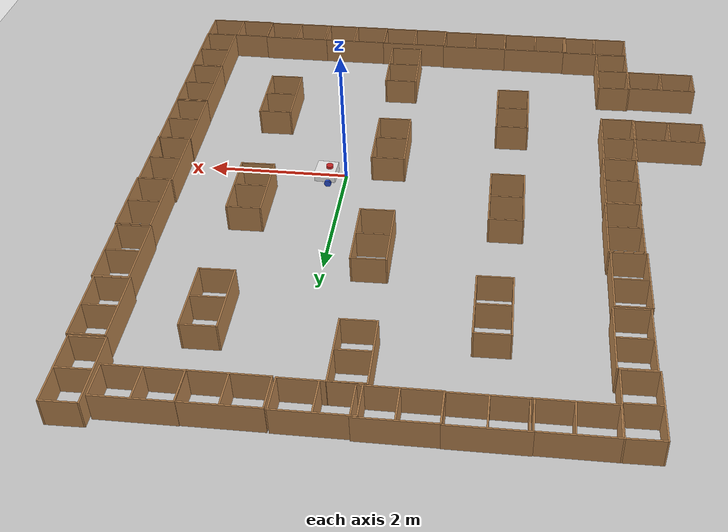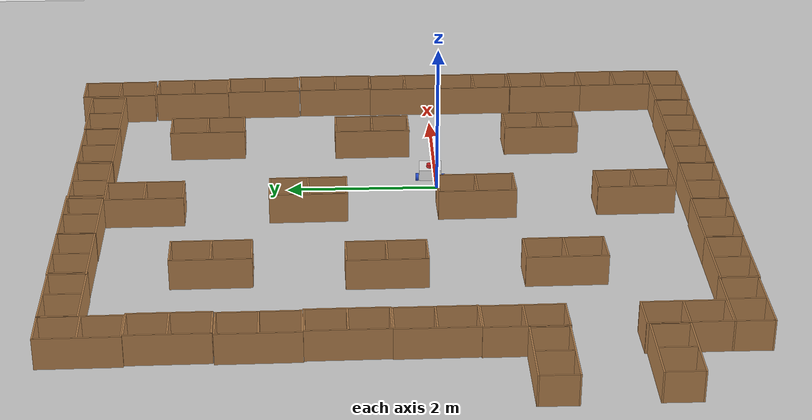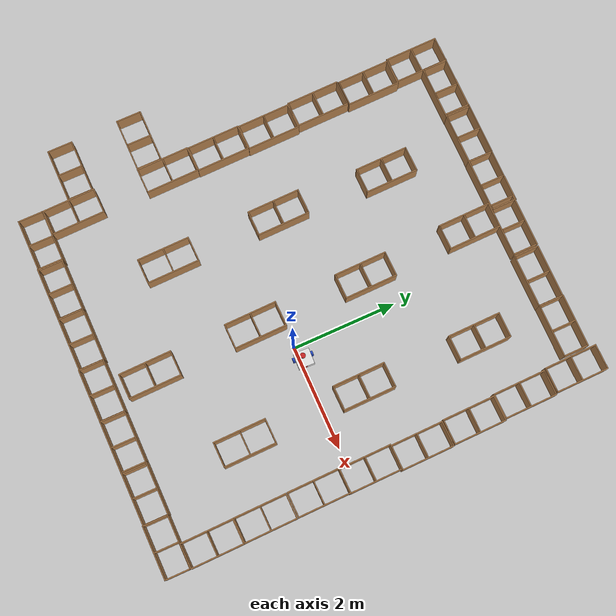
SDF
<sdf version="1.7">
 <world name="default">
  <light name="sun" type="directional">
   <pose>0 0 10 0 -0 0</pose>
   <diffuse>0.8 0.8 0.8 1</diffuse>
   <specular>0.2 0.2 0.2 1</specular>
   <attenuation>
    <range>1000</range>
    <constant>0.9</constant>
    <linear>0.01</linear>
    <quadratic>0.001</quadratic>
   </attenuation>
   <direction>-0.5 0.1 -0.9</direction>
   <spot><inner_angle>0</inner_angle><outer_angle>0</outer_angle><falloff>0</falloff></spot>
  </light>
  <model name="ground_plane">
   <static>1</static>
   <link name="link">
    <collision name="collision">
     <geometry><plane><normal>0 0 1</normal><size>100 100</size></plane></geometry>
     <surface>
      <contact><collide_bitmask>65535</collide_bitmask></contact>
      <friction><ode><mu>100</mu><mu2>50</mu2></ode></friction>
     </surface>
    </collision>
    <visual name="visual">
     <cast_shadows>0</cast_shadows>
     <geometry><plane><normal>0 0 1</normal><size>100 100</size></plane></geometry>
     <material>
      <script><uri>file://media/materials/scripts/gazebo.material</uri><name>Gazebo/Grey</name></script>
     </material>
    </visual>
   </link>
  </model>
  <gravity>0 0 -9.8</gravity>
  <magnetic_field>6e-06 2.3e-05 -4.2e-05</magnetic_field>
  <atmosphere type="adiabatic"/>
  <physics type="ode">
   <max_step_size>0.001</max_step_size>
   <real_time_factor>1</real_time_factor>
   <real_time_update_rate>1000</real_time_update_rate>
  </physics>
  <scene><ambient>0.4 0.4 0.4 1</ambient><background>0.7 0.7 0.7 1</background><shadows>1</shadows></scene>
  <audio><device>default</device></audio>
  <spherical_coordinates>
   <surface_model>EARTH_WGS84</surface_model>
   <latitude_deg>0</latitude_deg>
   <longitude_deg>0</longitude_deg>
   <elevation>0</elevation>
   <heading_deg>0</heading_deg>
  </spherical_coordinates>
  <model name="my_bot">
   <link name="base_link">
    <inertial>
     <pose>0.055714 0 0.078571 0 -0 0</pose>
     <mass>0.7</mass>
     <inertia>
      <ixx>0.0064169</ixx>
      <ixy>0</ixy>
      <ixz>0.00118929</ixz>
      <iyy>0.00745405</iyy>
      <iyz>0</iyz>
      <izz>0.00876214</izz>
     </inertia>
    </inertial>
    <collision name="base_link_fixed_joint_lump__chassis_collision">
     <pose>0.05 0 0.075 0 -0 0</pose>
     <geometry><box><size>0.3 0.3 0.15</size></box></geometry>
    </collision>
    <collision name="base_link_fixed_joint_lump__caster_wheel_collision_1">
     <pose>0.14 0 0 0 -0 0</pose>
     <geometry><sphere><radius>0.05</radius></sphere></geometry>
     <surface><friction><ode><mu>0.001</mu><mu2>0.001</mu2></ode></friction></surface>
    </collision>
    <collision name="base_link_fixed_joint_lump__laser_frame_collision_2">
     <pose>0 0 0.175 0 -0 0</pose>
     <geometry><cylinder><length>0.04</length><radius>0.05</radius></cylinder></geometry>
    </collision>
    <visual name="base_link_fixed_joint_lump__chassis_visual">
     <pose>0.05 0 0.075 0 -0 0</pose>
     <geometry><box><size>0.3 0.3 0.15</size></box></geometry>
     <material>
      <script><name>Gazebo/White</name><uri>file://media/materials/scripts/gazebo.material</uri></script>
     </material>
    </visual>
    <visual name="base_link_fixed_joint_lump__camera_link_visual_1">
     <pose>0.205 0 0.08 0 -0 0</pose>
     <geometry><box><size>0.01 0.03 0.03</size></box></geometry>
     <material>
      <script><name>Gazebo/Red</name><uri>file://media/materials/scripts/gazebo.material</uri></script>
     </material>
    </visual>
    <visual name="base_link_fixed_joint_lump__caster_wheel_visual_2">
     <pose>0.14 0 0 0 -0 0</pose>
     <geometry><sphere><radius>0.05</radius></sphere></geometry>
     <material>
      <script><name>Gazebo/Black</name><uri>file://media/materials/scripts/gazebo.material</uri></script>
     </material>
    </visual>
    <visual name="base_link_fixed_joint_lump__laser_frame_visual_3">
     <pose>0 0 0.175 0 -0 0</pose>
     <geometry><cylinder><length>0.04</length><radius>0.05</radius></cylinder></geometry>
     <material>
      <script><name>Gazebo/Red</name><uri>file://media/materials/scripts/gazebo.material</uri></script>
     </material>
    </visual>
    <sensor name="camera" type="camera">
     <visualize>1</visualize>
     <update_rate>10</update_rate>
     <camera>
      <horizontal_fov>1.089</horizontal_fov>
      <image><format>R8G8B8</format><width>640</width><height>480</height></image>
      <clip><near>0.05</near><far>8</far></clip>
     </camera>
     <plugin name="camera_controller" filename="libgazebo_ros_camera.so">
      <frame_name>camera_link_optical</frame_name>
     </plugin>
     <pose>0.205 0 0.08 0 -0 0</pose>
    </sensor>
    <sensor name="laser" type="ray">
     <visualize>1</visualize>
     <update_rate>10</update_rate>
     <ray>
      <scan>
       <horizontal>
        <samples>360</samples>
        <min_angle>-3.14</min_angle>
        <max_angle>3.14</max_angle>
        <resolution>1</resolution>
       </horizontal>
       <vertical><samples>1</samples><min_angle>0</min_angle><max_angle>0</max_angle></vertical>
      </scan>
      <range><min>0.3</min><max>12</max></range>
     </ray>
     <plugin name="laser_controller" filename="libgazebo_ros_ray_sensor.so">
      <ros><argument>~/out:=scan</argument></ros>
      <output_type>sensor_msgs/LaserScan</output_type>
      <frame_name>laser_frame</frame_name>
     </plugin>
     <pose>0 0 0.175 0 -0 0</pose>
    </sensor>
   </link>
   <joint name="left_wheel_joint" type="revolute">
    <pose relative_to="base_link">0 0.175 0 -1.5708 0 0</pose>
    <parent>base_link</parent>
    <child>left_wheel</child>
    <axis>
     <xyz>0 0 1</xyz>
     <limit><lower>-1e+16</lower><upper>1e+16</upper></limit>
     <dynamics><spring_reference>0</spring_reference><spring_stiffness>0</spring_stiffness></dynamics>
    </axis>
   </joint>
   <link name="left_wheel">
    <pose relative_to="left_wheel_joint">0 0 0 0 -0 0</pose>
    <inertial>
     <mass>0.1</mass>
     <inertia>
      <ixx>7.58333e-05</ixx>
      <ixy>0</ixy>
      <ixz>0</ixz>
      <iyy>7.58333e-05</iyy>
      <iyz>0</iyz>
      <izz>0.000125</izz>
     </inertia>
    </inertial>
    <collision name="left_wheel_collision">
     <geometry><cylinder><length>0.04</length><radius>0.05</radius></cylinder></geometry>
    </collision>
    <visual name="left_wheel_visual">
     <geometry><cylinder><length>0.04</length><radius>0.05</radius></cylinder></geometry>
     <material>
      <script><name>Gazebo/Blue</name><uri>file://media/materials/scripts/gazebo.material</uri></script>
     </material>
    </visual>
   </link>
   <joint name="right_wheel_joint" type="revolute">
    <pose relative_to="base_link">0 -0.175 0 1.5708 -0 0</pose>
    <parent>base_link</parent>
    <child>right_wheel</child>
    <axis>
     <xyz>0 0 -1</xyz>
     <limit><lower>-1e+16</lower><upper>1e+16</upper></limit>
     <dynamics><spring_reference>0</spring_reference><spring_stiffness>0</spring_stiffness></dynamics>
    </axis>
   </joint>
   <link name="right_wheel">
    <pose relative_to="right_wheel_joint">0 0 0 0 -0 0</pose>
    <inertial>
     <mass>0.1</mass>
     <inertia>
      <ixx>7.58333e-05</ixx>
      <ixy>0</ixy>
      <ixz>0</ixz>
      <iyy>7.58333e-05</iyy>
      <iyz>0</iyz>
      <izz>0.000125</izz>
     </inertia>
    </inertial>
    <collision name="right_wheel_collision">
     <geometry><cylinder><length>0.04</length><radius>0.05</radius></cylinder></geometry>
    </collision>
    <visual name="right_wheel_visual">
     <geometry><cylinder><length>0.04</length><radius>0.05</radius></cylinder></geometry>
     <material>
      <script><name>Gazebo/Blue</name><uri>file://media/materials/scripts/gazebo.material</uri></script>
     </material>
    </visual>
   </link>
   <static>0</static>
   <plugin name="diff_drive" filename="libgazebo_ros_diff_drive.so">
    <left_joint>left_wheel_joint</left_joint>
    <right_joint>right_wheel_joint</right_joint>
    <wheel_separation>0.35</wheel_separation>
    <wheel_diameter>0.1</wheel_diameter>
    <max_wheel_torque>200</max_wheel_torque>
    <max_wheel_acceleration>10.0</max_wheel_acceleration>
    <odometry_frame>odom</odometry_frame>
    <robot_base_frame>base_link</robot_base_frame>
    <publish_odom>1</publish_odom>
    <publish_odom_tf>1</publish_odom_tf>
    <publish_wheel_tf>1</publish_wheel_tf>
   </plugin>
   <pose>0.220586 0.080817 0.049995 2.8e-05 -4e-06 -0.051062</pose>
  </model>
  <model name="cabinet">
   <static>1</static>
   <link name="cabinet_bottom_plate">
    <inertial>
     <pose>0 0 -1 0 -0 0</pose>
     <inertia><ixx>2.05</ixx><ixy>0</ixy><ixz>0</ixz><iyy>2.05</iyy><iyz>0</iyz><izz>2.05</izz></inertia>
     <mass>25</mass>
    </inertial>
    <collision name="cabinet_bottom_plate_geom">
     <pose>0 0 0.01 0 -0 0</pose>
     <geometry><box><size>0.45 0.45 0.02</size></box></geometry>
    </collision>
    <visual name="cabinet_bottom_plate_geom_visual">
     <pose>0 0 0.01 0 -0 0</pose>
     <geometry><box><size>0.45 0.45 0.02</size></box></geometry>
     <material>
      <script><uri>file://media/materials/scripts/gazebo.material</uri><name>Gazebo/Wood</name></script>
     </material>
    </visual>
    <collision name="cabinet_bottom_plate_geom_cabinet_back_plate">
     <pose>0.235 0 0.51 0 -0 0</pose>
     <geometry><box><size>0.02 0.45 1.02</size></box></geometry>
    </collision>
    <visual name="cabinet_bottom_plate_geom_cabinet_back_plate_visual">
     <pose>0.235 0 0.51 0 -0 0</pose>
     <geometry><box><size>0.02 0.45 1.02</size></box></geometry>
     <material>
      <script><uri>file://media/materials/scripts/gazebo.material</uri><name>Gazebo/Wood</name></script>
     </material>
    </visual>
    <collision name="cabinet_bottom_plate_geom_cabinet_left_plate">
     <pose>0 0.235 0.51 0 -0 0</pose>
     <geometry><box><size>0.45 0.02 1.02</size></box></geometry>
    </collision>
    <visual name="cabinet_bottom_plate_geom_cabinet_left_plate_visual">
     <pose>0 0.235 0.51 0 -0 0</pose>
     <geometry><box><size>0.45 0.02 1.02</size></box></geometry>
     <material>
      <script><uri>file://media/materials/scripts/gazebo.material</uri><name>Gazebo/Wood</name></script>
     </material>
    </visual>
    <collision name="cabinet_bottom_plate_geom_cabinet_middle_plate">
     <pose>0 0 0.51 0 -0 0</pose>
     <geometry><box><size>0.45 0.45 0.02</size></box></geometry>
    </collision>
    <visual name="cabinet_bottom_plate_geom_cabinet_middle_plate_visual">
     <pose>0 0 0.51 0 -0 0</pose>
     <geometry><box><size>0.45 0.45 0.02</size></box></geometry>
     <material>
      <script><uri>file://media/materials/scripts/gazebo.material</uri><name>Gazebo/Wood</name></script>
     </material>
    </visual>
    <collision name="cabinet_bottom_plate_geom_cabinet_right_plate">
     <pose>0 -0.235 0.51 0 -0 0</pose>
     <geometry><box><size>0.45 0.02 1.02</size></box></geometry>
    </collision>
    <visual name="cabinet_bottom_plate_geom_cabinet_right_plate_visual">
     <pose>0 -0.235 0.51 0 -0 0</pose>
     <geometry><box><size>0.45 0.02 1.02</size></box></geometry>
     <material>
      <script><uri>file://media/materials/scripts/gazebo.material</uri><name>Gazebo/Wood</name></script>
     </material>
    </visual>
    <collision name="cabinet_bottom_plate_geom_cabinet_top_plate">
     <pose>0 0 1.01 0 -0 0</pose>
     <geometry><box><size>0.45 0.45 0.02</size></box></geometry>
    </collision>
    <visual name="cabinet_bottom_plate_geom_cabinet_top_plate_visual">
     <pose>0 0 1.01 0 -0 0</pose>
     <geometry><box><size>0.45 0.45 0.02</size></box></geometry>
     <material>
      <script><uri>file://media/materials/scripts/gazebo.material</uri><name>Gazebo/Wood</name></script>
     </material>
    </visual>
   </link>
   <pose>-0.147311 -3.44738 0.169718 3.14159 1.5658 3.14159</pose>
  </model>
  <model name="cabinet_clone">
   <static>1</static>
   <link name="cabinet_bottom_plate">
    <inertial>
     <pose>0 0 -1 0 -0 0</pose>
     <inertia><ixx>2.05</ixx><ixy>0</ixy><ixz>0</ixz><iyy>2.05</iyy><iyz>0</iyz><izz>2.05</izz></inertia>
     <mass>25</mass>
    </inertial>
    <collision name="cabinet_bottom_plate_geom">
     <pose>0 0 0.01 0 -0 0</pose>
     <geometry><box><size>0.45 0.45 0.02</size></box></geometry>
    </collision>
    <visual name="cabinet_bottom_plate_geom_visual">
     <pose>0 0 0.01 0 -0 0</pose>
     <geometry><box><size>0.45 0.45 0.02</size></box></geometry>
     <material>
      <script><uri>file://media/materials/scripts/gazebo.material</uri><name>Gazebo/Wood</name></script>
     </material>
    </visual>
    <collision name="cabinet_bottom_plate_geom_cabinet_back_plate">
     <pose>0.235 0 0.51 0 -0 0</pose>
     <geometry><box><size>0.02 0.45 1.02</size></box></geometry>
    </collision>
    <visual name="cabinet_bottom_plate_geom_cabinet_back_plate_visual">
     <pose>0.235 0 0.51 0 -0 0</pose>
     <geometry><box><size>0.02 0.45 1.02</size></box></geometry>
     <material>
      <script><uri>file://media/materials/scripts/gazebo.material</uri><name>Gazebo/Wood</name></script>
     </material>
    </visual>
    <collision name="cabinet_bottom_plate_geom_cabinet_left_plate">
     <pose>0 0.235 0.51 0 -0 0</pose>
     <geometry><box><size>0.45 0.02 1.02</size></box></geometry>
    </collision>
    <visual name="cabinet_bottom_plate_geom_cabinet_left_plate_visual">
     <pose>0 0.235 0.51 0 -0 0</pose>
     <geometry><box><size>0.45 0.02 1.02</size></box></geometry>
     <material>
      <script><uri>file://media/materials/scripts/gazebo.material</uri><name>Gazebo/Wood</name></script>
     </material>
    </visual>
    <collision name="cabinet_bottom_plate_geom_cabinet_middle_plate">
     <pose>0 0 0.51 0 -0 0</pose>
     <geometry><box><size>0.45 0.45 0.02</size></box></geometry>
    </collision>
    <visual name="cabinet_bottom_plate_geom_cabinet_middle_plate_visual">
     <pose>0 0 0.51 0 -0 0</pose>
     <geometry><box><size>0.45 0.45 0.02</size></box></geometry>
     <material>
      <script><uri>file://media/materials/scripts/gazebo.material</uri><name>Gazebo/Wood</name></script>
     </material>
    </visual>
    <collision name="cabinet_bottom_plate_geom_cabinet_right_plate">
     <pose>0 -0.235 0.51 0 -0 0</pose>
     <geometry><box><size>0.45 0.02 1.02</size></box></geometry>
    </collision>
    <visual name="cabinet_bottom_plate_geom_cabinet_right_plate_visual">
     <pose>0 -0.235 0.51 0 -0 0</pose>
     <geometry><box><size>0.45 0.02 1.02</size></box></geometry>
     <material>
      <script><uri>file://media/materials/scripts/gazebo.material</uri><name>Gazebo/Wood</name></script>
     </material>
    </visual>
    <collision name="cabinet_bottom_plate_geom_cabinet_top_plate">
     <pose>0 0 1.01 0 -0 0</pose>
     <geometry><box><size>0.45 0.45 0.02</size></box></geometry>
    </collision>
    <visual name="cabinet_bottom_plate_geom_cabinet_top_plate_visual">
     <pose>0 0 1.01 0 -0 0</pose>
     <geometry><box><size>0.45 0.45 0.02</size></box></geometry>
     <material>
      <script><uri>file://media/materials/scripts/gazebo.material</uri><name>Gazebo/Wood</name></script>
     </material>
    </visual>
   </link>
   <pose>-1.15505 -3.44663 0.169718 3.14159 1.5658 3.14159</pose>
  </model>
  <model name="cabinet_clone_0">
   <static>1</static>
   <link name="cabinet_bottom_plate">
    <inertial>
     <pose>0 0 -1 0 -0 0</pose>
     <inertia><ixx>2.05</ixx><ixy>0</ixy><ixz>0</ixz><iyy>2.05</iyy><iyz>0</iyz><izz>2.05</izz></inertia>
     <mass>25</mass>
    </inertial>
    <collision name="cabinet_bottom_plate_geom">
     <pose>0 0 0.01 0 -0 0</pose>
     <geometry><box><size>0.45 0.45 0.02</size></box></geometry>
    </collision>
    <visual name="cabinet_bottom_plate_geom_visual">
     <pose>0 0 0.01 0 -0 0</pose>
     <geometry><box><size>0.45 0.45 0.02</size></box></geometry>
     <material>
      <script><uri>file://media/materials/scripts/gazebo.material</uri><name>Gazebo/Wood</name></script>
     </material>
    </visual>
    <collision name="cabinet_bottom_plate_geom_cabinet_back_plate">
     <pose>0.235 0 0.51 0 -0 0</pose>
     <geometry><box><size>0.02 0.45 1.02</size></box></geometry>
    </collision>
    <visual name="cabinet_bottom_plate_geom_cabinet_back_plate_visual">
     <pose>0.235 0 0.51 0 -0 0</pose>
     <geometry><box><size>0.02 0.45 1.02</size></box></geometry>
     <material>
      <script><uri>file://media/materials/scripts/gazebo.material</uri><name>Gazebo/Wood</name></script>
     </material>
    </visual>
    <collision name="cabinet_bottom_plate_geom_cabinet_left_plate">
     <pose>0 0.235 0.51 0 -0 0</pose>
     <geometry><box><size>0.45 0.02 1.02</size></box></geometry>
    </collision>
    <visual name="cabinet_bottom_plate_geom_cabinet_left_plate_visual">
     <pose>0 0.235 0.51 0 -0 0</pose>
     <geometry><box><size>0.45 0.02 1.02</size></box></geometry>
     <material>
      <script><uri>file://media/materials/scripts/gazebo.material</uri><name>Gazebo/Wood</name></script>
     </material>
    </visual>
    <collision name="cabinet_bottom_plate_geom_cabinet_middle_plate">
     <pose>0 0 0.51 0 -0 0</pose>
     <geometry><box><size>0.45 0.45 0.02</size></box></geometry>
    </collision>
    <visual name="cabinet_bottom_plate_geom_cabinet_middle_plate_visual">
     <pose>0 0 0.51 0 -0 0</pose>
     <geometry><box><size>0.45 0.45 0.02</size></box></geometry>
     <material>
      <script><uri>file://media/materials/scripts/gazebo.material</uri><name>Gazebo/Wood</name></script>
     </material>
    </visual>
    <collision name="cabinet_bottom_plate_geom_cabinet_right_plate">
     <pose>0 -0.235 0.51 0 -0 0</pose>
     <geometry><box><size>0.45 0.02 1.02</size></box></geometry>
    </collision>
    <visual name="cabinet_bottom_plate_geom_cabinet_right_plate_visual">
     <pose>0 -0.235 0.51 0 -0 0</pose>
     <geometry><box><size>0.45 0.02 1.02</size></box></geometry>
     <material>
      <script><uri>file://media/materials/scripts/gazebo.material</uri><name>Gazebo/Wood</name></script>
     </material>
    </visual>
    <collision name="cabinet_bottom_plate_geom_cabinet_top_plate">
     <pose>0 0 1.01 0 -0 0</pose>
     <geometry><box><size>0.45 0.45 0.02</size></box></geometry>
    </collision>
    <visual name="cabinet_bottom_plate_geom_cabinet_top_plate_visual">
     <pose>0 0 1.01 0 -0 0</pose>
     <geometry><box><size>0.45 0.45 0.02</size></box></geometry>
     <material>
      <script><uri>file://media/materials/scripts/gazebo.material</uri><name>Gazebo/Wood</name></script>
     </material>
    </visual>
   </link>
   <pose>-2.16153 -3.43466 0.169718 3.14159 1.5658 3.14159</pose>
  </model>
  <model name="cabinet_clone_1">
   <static>1</static>
   <link name="cabinet_bottom_plate">
    <inertial>
     <pose>0 0 -1 0 -0 0</pose>
     <inertia><ixx>2.05</ixx><ixy>0</ixy><ixz>0</ixz><iyy>2.05</iyy><iyz>0</iyz><izz>2.05</izz></inertia>
     <mass>25</mass>
    </inertial>
    <collision name="cabinet_bottom_plate_geom">
     <pose>0 0 0.01 0 -0 0</pose>
     <geometry><box><size>0.45 0.45 0.02</size></box></geometry>
    </collision>
    <visual name="cabinet_bottom_plate_geom_visual">
     <pose>0 0 0.01 0 -0 0</pose>
     <geometry><box><size>0.45 0.45 0.02</size></box></geometry>
     <material>
      <script><uri>file://media/materials/scripts/gazebo.material</uri><name>Gazebo/Wood</name></script>
     </material>
    </visual>
    <collision name="cabinet_bottom_plate_geom_cabinet_back_plate">
     <pose>0.235 0 0.51 0 -0 0</pose>
     <geometry><box><size>0.02 0.45 1.02</size></box></geometry>
    </collision>
    <visual name="cabinet_bottom_plate_geom_cabinet_back_plate_visual">
     <pose>0.235 0 0.51 0 -0 0</pose>
     <geometry><box><size>0.02 0.45 1.02</size></box></geometry>
     <material>
      <script><uri>file://media/materials/scripts/gazebo.material</uri><name>Gazebo/Wood</name></script>
     </material>
    </visual>
    <collision name="cabinet_bottom_plate_geom_cabinet_left_plate">
     <pose>0 0.235 0.51 0 -0 0</pose>
     <geometry><box><size>0.45 0.02 1.02</size></box></geometry>
    </collision>
    <visual name="cabinet_bottom_plate_geom_cabinet_left_plate_visual">
     <pose>0 0.235 0.51 0 -0 0</pose>
     <geometry><box><size>0.45 0.02 1.02</size></box></geometry>
     <material>
      <script><uri>file://media/materials/scripts/gazebo.material</uri><name>Gazebo/Wood</name></script>
     </material>
    </visual>
    <collision name="cabinet_bottom_plate_geom_cabinet_middle_plate">
     <pose>0 0 0.51 0 -0 0</pose>
     <geometry><box><size>0.45 0.45 0.02</size></box></geometry>
    </collision>
    <visual name="cabinet_bottom_plate_geom_cabinet_middle_plate_visual">
     <pose>0 0 0.51 0 -0 0</pose>
     <geometry><box><size>0.45 0.45 0.02</size></box></geometry>
     <material>
      <script><uri>file://media/materials/scripts/gazebo.material</uri><name>Gazebo/Wood</name></script>
     </material>
    </visual>
    <collision name="cabinet_bottom_plate_geom_cabinet_right_plate">
     <pose>0 -0.235 0.51 0 -0 0</pose>
     <geometry><box><size>0.45 0.02 1.02</size></box></geometry>
    </collision>
    <visual name="cabinet_bottom_plate_geom_cabinet_right_plate_visual">
     <pose>0 -0.235 0.51 0 -0 0</pose>
     <geometry><box><size>0.45 0.02 1.02</size></box></geometry>
     <material>
      <script><uri>file://media/materials/scripts/gazebo.material</uri><name>Gazebo/Wood</name></script>
     </material>
    </visual>
    <collision name="cabinet_bottom_plate_geom_cabinet_top_plate">
     <pose>0 0 1.01 0 -0 0</pose>
     <geometry><box><size>0.45 0.45 0.02</size></box></geometry>
    </collision>
    <visual name="cabinet_bottom_plate_geom_cabinet_top_plate_visual">
     <pose>0 0 1.01 0 -0 0</pose>
     <geometry><box><size>0.45 0.45 0.02</size></box></geometry>
     <material>
      <script><uri>file://media/materials/scripts/gazebo.material</uri><name>Gazebo/Wood</name></script>
     </material>
    </visual>
   </link>
   <pose>-3.17096 -3.43522 0.169718 3.14159 1.5658 3.14159</pose>
  </model>
  <model name="cabinet_clone_2">
   <static>1</static>
   <link name="cabinet_bottom_plate">
    <inertial>
     <pose>0 0 -1 0 -0 0</pose>
     <inertia><ixx>2.05</ixx><ixy>0</ixy><ixz>0</ixz><iyy>2.05</iyy><iyz>0</iyz><izz>2.05</izz></inertia>
     <mass>25</mass>
    </inertial>
    <collision name="cabinet_bottom_plate_geom">
     <pose>0 0 0.01 0 -0 0</pose>
     <geometry><box><size>0.45 0.45 0.02</size></box></geometry>
    </collision>
    <visual name="cabinet_bottom_plate_geom_visual">
     <pose>0 0 0.01 0 -0 0</pose>
     <geometry><box><size>0.45 0.45 0.02</size></box></geometry>
     <material>
      <script><uri>file://media/materials/scripts/gazebo.material</uri><name>Gazebo/Wood</name></script>
     </material>
    </visual>
    <collision name="cabinet_bottom_plate_geom_cabinet_back_plate">
     <pose>0.235 0 0.51 0 -0 0</pose>
     <geometry><box><size>0.02 0.45 1.02</size></box></geometry>
    </collision>
    <visual name="cabinet_bottom_plate_geom_cabinet_back_plate_visual">
     <pose>0.235 0 0.51 0 -0 0</pose>
     <geometry><box><size>0.02 0.45 1.02</size></box></geometry>
     <material>
      <script><uri>file://media/materials/scripts/gazebo.material</uri><name>Gazebo/Wood</name></script>
     </material>
    </visual>
    <collision name="cabinet_bottom_plate_geom_cabinet_left_plate">
     <pose>0 0.235 0.51 0 -0 0</pose>
     <geometry><box><size>0.45 0.02 1.02</size></box></geometry>
    </collision>
    <visual name="cabinet_bottom_plate_geom_cabinet_left_plate_visual">
     <pose>0 0.235 0.51 0 -0 0</pose>
     <geometry><box><size>0.45 0.02 1.02</size></box></geometry>
     <material>
      <script><uri>file://media/materials/scripts/gazebo.material</uri><name>Gazebo/Wood</name></script>
     </material>
    </visual>
    <collision name="cabinet_bottom_plate_geom_cabinet_middle_plate">
     <pose>0 0 0.51 0 -0 0</pose>
     <geometry><box><size>0.45 0.45 0.02</size></box></geometry>
    </collision>
    <visual name="cabinet_bottom_plate_geom_cabinet_middle_plate_visual">
     <pose>0 0 0.51 0 -0 0</pose>
     <geometry><box><size>0.45 0.45 0.02</size></box></geometry>
     <material>
      <script><uri>file://media/materials/scripts/gazebo.material</uri><name>Gazebo/Wood</name></script>
     </material>
    </visual>
    <collision name="cabinet_bottom_plate_geom_cabinet_right_plate">
     <pose>0 -0.235 0.51 0 -0 0</pose>
     <geometry><box><size>0.45 0.02 1.02</size></box></geometry>
    </collision>
    <visual name="cabinet_bottom_plate_geom_cabinet_right_plate_visual">
     <pose>0 -0.235 0.51 0 -0 0</pose>
     <geometry><box><size>0.45 0.02 1.02</size></box></geometry>
     <material>
      <script><uri>file://media/materials/scripts/gazebo.material</uri><name>Gazebo/Wood</name></script>
     </material>
    </visual>
    <collision name="cabinet_bottom_plate_geom_cabinet_top_plate">
     <pose>0 0 1.01 0 -0 0</pose>
     <geometry><box><size>0.45 0.45 0.02</size></box></geometry>
    </collision>
    <visual name="cabinet_bottom_plate_geom_cabinet_top_plate_visual">
     <pose>0 0 1.01 0 -0 0</pose>
     <geometry><box><size>0.45 0.45 0.02</size></box></geometry>
     <material>
      <script><uri>file://media/materials/scripts/gazebo.material</uri><name>Gazebo/Wood</name></script>
     </material>
    </visual>
   </link>
   <pose>-4.14701 -3.42325 0.169718 3.14159 1.5658 3.14159</pose>
  </model>
  <model name="cabinet_clone_3">
   <static>1</static>
   <link name="cabinet_bottom_plate">
    <inertial>
     <pose>0 0 -1 0 -0 0</pose>
     <inertia><ixx>2.05</ixx><ixy>0</ixy><ixz>0</ixz><iyy>2.05</iyy><iyz>0</iyz><izz>2.05</izz></inertia>
     <mass>25</mass>
    </inertial>
    <collision name="cabinet_bottom_plate_geom">
     <pose>0 0 0.01 0 -0 0</pose>
     <geometry><box><size>0.45 0.45 0.02</size></box></geometry>
    </collision>
    <visual name="cabinet_bottom_plate_geom_visual">
     <pose>0 0 0.01 0 -0 0</pose>
     <geometry><box><size>0.45 0.45 0.02</size></box></geometry>
     <material>
      <script><uri>file://media/materials/scripts/gazebo.material</uri><name>Gazebo/Wood</name></script>
     </material>
    </visual>
    <collision name="cabinet_bottom_plate_geom_cabinet_back_plate">
     <pose>0.235 0 0.51 0 -0 0</pose>
     <geometry><box><size>0.02 0.45 1.02</size></box></geometry>
    </collision>
    <visual name="cabinet_bottom_plate_geom_cabinet_back_plate_visual">
     <pose>0.235 0 0.51 0 -0 0</pose>
     <geometry><box><size>0.02 0.45 1.02</size></box></geometry>
     <material>
      <script><uri>file://media/materials/scripts/gazebo.material</uri><name>Gazebo/Wood</name></script>
     </material>
    </visual>
    <collision name="cabinet_bottom_plate_geom_cabinet_left_plate">
     <pose>0 0.235 0.51 0 -0 0</pose>
     <geometry><box><size>0.45 0.02 1.02</size></box></geometry>
    </collision>
    <visual name="cabinet_bottom_plate_geom_cabinet_left_plate_visual">
     <pose>0 0.235 0.51 0 -0 0</pose>
     <geometry><box><size>0.45 0.02 1.02</size></box></geometry>
     <material>
      <script><uri>file://media/materials/scripts/gazebo.material</uri><name>Gazebo/Wood</name></script>
     </material>
    </visual>
    <collision name="cabinet_bottom_plate_geom_cabinet_middle_plate">
     <pose>0 0 0.51 0 -0 0</pose>
     <geometry><box><size>0.45 0.45 0.02</size></box></geometry>
    </collision>
    <visual name="cabinet_bottom_plate_geom_cabinet_middle_plate_visual">
     <pose>0 0 0.51 0 -0 0</pose>
     <geometry><box><size>0.45 0.45 0.02</size></box></geometry>
     <material>
      <script><uri>file://media/materials/scripts/gazebo.material</uri><name>Gazebo/Wood</name></script>
     </material>
    </visual>
    <collision name="cabinet_bottom_plate_geom_cabinet_right_plate">
     <pose>0 -0.235 0.51 0 -0 0</pose>
     <geometry><box><size>0.45 0.02 1.02</size></box></geometry>
    </collision>
    <visual name="cabinet_bottom_plate_geom_cabinet_right_plate_visual">
     <pose>0 -0.235 0.51 0 -0 0</pose>
     <geometry><box><size>0.45 0.02 1.02</size></box></geometry>
     <material>
      <script><uri>file://media/materials/scripts/gazebo.material</uri><name>Gazebo/Wood</name></script>
     </material>
    </visual>
    <collision name="cabinet_bottom_plate_geom_cabinet_top_plate">
     <pose>0 0 1.01 0 -0 0</pose>
     <geometry><box><size>0.45 0.45 0.02</size></box></geometry>
    </collision>
    <visual name="cabinet_bottom_plate_geom_cabinet_top_plate_visual">
     <pose>0 0 1.01 0 -0 0</pose>
     <geometry><box><size>0.45 0.45 0.02</size></box></geometry>
     <material>
      <script><uri>file://media/materials/scripts/gazebo.material</uri><name>Gazebo/Wood</name></script>
     </material>
    </visual>
   </link>
   <pose>0.824331 -3.4453 0.169718 3.14159 1.5658 3.14159</pose>
  </model>
  <model name="cabinet_clone_4">
   <static>1</static>
   <link name="cabinet_bottom_plate">
    <inertial>
     <pose>0 0 -1 0 -0 0</pose>
     <inertia><ixx>2.05</ixx><ixy>0</ixy><ixz>0</ixz><iyy>2.05</iyy><iyz>0</iyz><izz>2.05</izz></inertia>
     <mass>25</mass>
    </inertial>
    <collision name="cabinet_bottom_plate_geom">
     <pose>0 0 0.01 0 -0 0</pose>
     <geometry><box><size>0.45 0.45 0.02</size></box></geometry>
    </collision>
    <visual name="cabinet_bottom_plate_geom_visual">
     <pose>0 0 0.01 0 -0 0</pose>
     <geometry><box><size>0.45 0.45 0.02</size></box></geometry>
     <material>
      <script><uri>file://media/materials/scripts/gazebo.material</uri><name>Gazebo/Wood</name></script>
     </material>
    </visual>
    <collision name="cabinet_bottom_plate_geom_cabinet_back_plate">
     <pose>0.235 0 0.51 0 -0 0</pose>
     <geometry><box><size>0.02 0.45 1.02</size></box></geometry>
    </collision>
    <visual name="cabinet_bottom_plate_geom_cabinet_back_plate_visual">
     <pose>0.235 0 0.51 0 -0 0</pose>
     <geometry><box><size>0.02 0.45 1.02</size></box></geometry>
     <material>
      <script><uri>file://media/materials/scripts/gazebo.material</uri><name>Gazebo/Wood</name></script>
     </material>
    </visual>
    <collision name="cabinet_bottom_plate_geom_cabinet_left_plate">
     <pose>0 0.235 0.51 0 -0 0</pose>
     <geometry><box><size>0.45 0.02 1.02</size></box></geometry>
    </collision>
    <visual name="cabinet_bottom_plate_geom_cabinet_left_plate_visual">
     <pose>0 0.235 0.51 0 -0 0</pose>
     <geometry><box><size>0.45 0.02 1.02</size></box></geometry>
     <material>
      <script><uri>file://media/materials/scripts/gazebo.material</uri><name>Gazebo/Wood</name></script>
     </material>
    </visual>
    <collision name="cabinet_bottom_plate_geom_cabinet_middle_plate">
     <pose>0 0 0.51 0 -0 0</pose>
     <geometry><box><size>0.45 0.45 0.02</size></box></geometry>
    </collision>
    <visual name="cabinet_bottom_plate_geom_cabinet_middle_plate_visual">
     <pose>0 0 0.51 0 -0 0</pose>
     <geometry><box><size>0.45 0.45 0.02</size></box></geometry>
     <material>
      <script><uri>file://media/materials/scripts/gazebo.material</uri><name>Gazebo/Wood</name></script>
     </material>
    </visual>
    <collision name="cabinet_bottom_plate_geom_cabinet_right_plate">
     <pose>0 -0.235 0.51 0 -0 0</pose>
     <geometry><box><size>0.45 0.02 1.02</size></box></geometry>
    </collision>
    <visual name="cabinet_bottom_plate_geom_cabinet_right_plate_visual">
     <pose>0 -0.235 0.51 0 -0 0</pose>
     <geometry><box><size>0.45 0.02 1.02</size></box></geometry>
     <material>
      <script><uri>file://media/materials/scripts/gazebo.material</uri><name>Gazebo/Wood</name></script>
     </material>
    </visual>
    <collision name="cabinet_bottom_plate_geom_cabinet_top_plate">
     <pose>0 0 1.01 0 -0 0</pose>
     <geometry><box><size>0.45 0.45 0.02</size></box></geometry>
    </collision>
    <visual name="cabinet_bottom_plate_geom_cabinet_top_plate_visual">
     <pose>0 0 1.01 0 -0 0</pose>
     <geometry><box><size>0.45 0.45 0.02</size></box></geometry>
     <material>
      <script><uri>file://media/materials/scripts/gazebo.material</uri><name>Gazebo/Wood</name></script>
     </material>
    </visual>
   </link>
   <pose>1.83361 -3.45652 0.169718 3.14159 1.5658 3.14159</pose>
  </model>
  <model name="cabinet_clone_6">
   <static>1</static>
   <link name="cabinet_bottom_plate">
    <inertial>
     <pose>0 0 -1 0 -0 0</pose>
     <inertia><ixx>2.05</ixx><ixy>0</ixy><ixz>0</ixz><iyy>2.05</iyy><iyz>0</iyz><izz>2.05</izz></inertia>
     <mass>25</mass>
    </inertial>
    <collision name="cabinet_bottom_plate_geom">
     <pose>0 0 0.01 0 -0 0</pose>
     <geometry><box><size>0.45 0.45 0.02</size></box></geometry>
    </collision>
    <visual name="cabinet_bottom_plate_geom_visual">
     <pose>0 0 0.01 0 -0 0</pose>
     <geometry><box><size>0.45 0.45 0.02</size></box></geometry>
     <material>
      <script><uri>file://media/materials/scripts/gazebo.material</uri><name>Gazebo/Wood</name></script>
     </material>
    </visual>
    <collision name="cabinet_bottom_plate_geom_cabinet_back_plate">
     <pose>0.235 0 0.51 0 -0 0</pose>
     <geometry><box><size>0.02 0.45 1.02</size></box></geometry>
    </collision>
    <visual name="cabinet_bottom_plate_geom_cabinet_back_plate_visual">
     <pose>0.235 0 0.51 0 -0 0</pose>
     <geometry><box><size>0.02 0.45 1.02</size></box></geometry>
     <material>
      <script><uri>file://media/materials/scripts/gazebo.material</uri><name>Gazebo/Wood</name></script>
     </material>
    </visual>
    <collision name="cabinet_bottom_plate_geom_cabinet_left_plate">
     <pose>0 0.235 0.51 0 -0 0</pose>
     <geometry><box><size>0.45 0.02 1.02</size></box></geometry>
    </collision>
    <visual name="cabinet_bottom_plate_geom_cabinet_left_plate_visual">
     <pose>0 0.235 0.51 0 -0 0</pose>
     <geometry><box><size>0.45 0.02 1.02</size></box></geometry>
     <material>
      <script><uri>file://media/materials/scripts/gazebo.material</uri><name>Gazebo/Wood</name></script>
     </material>
    </visual>
    <collision name="cabinet_bottom_plate_geom_cabinet_middle_plate">
     <pose>0 0 0.51 0 -0 0</pose>
     <geometry><box><size>0.45 0.45 0.02</size></box></geometry>
    </collision>
    <visual name="cabinet_bottom_plate_geom_cabinet_middle_plate_visual">
     <pose>0 0 0.51 0 -0 0</pose>
     <geometry><box><size>0.45 0.45 0.02</size></box></geometry>
     <material>
      <script><uri>file://media/materials/scripts/gazebo.material</uri><name>Gazebo/Wood</name></script>
     </material>
    </visual>
    <collision name="cabinet_bottom_plate_geom_cabinet_right_plate">
     <pose>0 -0.235 0.51 0 -0 0</pose>
     <geometry><box><size>0.45 0.02 1.02</size></box></geometry>
    </collision>
    <visual name="cabinet_bottom_plate_geom_cabinet_right_plate_visual">
     <pose>0 -0.235 0.51 0 -0 0</pose>
     <geometry><box><size>0.45 0.02 1.02</size></box></geometry>
     <material>
      <script><uri>file://media/materials/scripts/gazebo.material</uri><name>Gazebo/Wood</name></script>
     </material>
    </visual>
    <collision name="cabinet_bottom_plate_geom_cabinet_top_plate">
     <pose>0 0 1.01 0 -0 0</pose>
     <geometry><box><size>0.45 0.45 0.02</size></box></geometry>
    </collision>
    <visual name="cabinet_bottom_plate_geom_cabinet_top_plate_visual">
     <pose>0 0 1.01 0 -0 0</pose>
     <geometry><box><size>0.45 0.45 0.02</size></box></geometry>
     <material>
      <script><uri>file://media/materials/scripts/gazebo.material</uri><name>Gazebo/Wood</name></script>
     </material>
    </visual>
   </link>
   <pose>-5.17054 -2.43861 0.169718 3.14159 1.5658 3.14159</pose>
  </model>
  <model name="cabinet_clone_7">
   <static>1</static>
   <link name="cabinet_bottom_plate">
    <inertial>
     <pose>0 0 -1 0 -0 0</pose>
     <inertia><ixx>2.05</ixx><ixy>0</ixy><ixz>0</ixz><iyy>2.05</iyy><iyz>0</iyz><izz>2.05</izz></inertia>
     <mass>25</mass>
    </inertial>
    <collision name="cabinet_bottom_plate_geom">
     <pose>0 0 0.01 0 -0 0</pose>
     <geometry><box><size>0.45 0.45 0.02</size></box></geometry>
    </collision>
    <visual name="cabinet_bottom_plate_geom_visual">
     <pose>0 0 0.01 0 -0 0</pose>
     <geometry><box><size>0.45 0.45 0.02</size></box></geometry>
     <material>
      <script><uri>file://media/materials/scripts/gazebo.material</uri><name>Gazebo/Wood</name></script>
     </material>
    </visual>
    <collision name="cabinet_bottom_plate_geom_cabinet_back_plate">
     <pose>0.235 0 0.51 0 -0 0</pose>
     <geometry><box><size>0.02 0.45 1.02</size></box></geometry>
    </collision>
    <visual name="cabinet_bottom_plate_geom_cabinet_back_plate_visual">
     <pose>0.235 0 0.51 0 -0 0</pose>
     <geometry><box><size>0.02 0.45 1.02</size></box></geometry>
     <material>
      <script><uri>file://media/materials/scripts/gazebo.material</uri><name>Gazebo/Wood</name></script>
     </material>
    </visual>
    <collision name="cabinet_bottom_plate_geom_cabinet_left_plate">
     <pose>0 0.235 0.51 0 -0 0</pose>
     <geometry><box><size>0.45 0.02 1.02</size></box></geometry>
    </collision>
    <visual name="cabinet_bottom_plate_geom_cabinet_left_plate_visual">
     <pose>0 0.235 0.51 0 -0 0</pose>
     <geometry><box><size>0.45 0.02 1.02</size></box></geometry>
     <material>
      <script><uri>file://media/materials/scripts/gazebo.material</uri><name>Gazebo/Wood</name></script>
     </material>
    </visual>
    <collision name="cabinet_bottom_plate_geom_cabinet_middle_plate">
     <pose>0 0 0.51 0 -0 0</pose>
     <geometry><box><size>0.45 0.45 0.02</size></box></geometry>
    </collision>
    <visual name="cabinet_bottom_plate_geom_cabinet_middle_plate_visual">
     <pose>0 0 0.51 0 -0 0</pose>
     <geometry><box><size>0.45 0.45 0.02</size></box></geometry>
     <material>
      <script><uri>file://media/materials/scripts/gazebo.material</uri><name>Gazebo/Wood</name></script>
     </material>
    </visual>
    <collision name="cabinet_bottom_plate_geom_cabinet_right_plate">
     <pose>0 -0.235 0.51 0 -0 0</pose>
     <geometry><box><size>0.45 0.02 1.02</size></box></geometry>
    </collision>
    <visual name="cabinet_bottom_plate_geom_cabinet_right_plate_visual">
     <pose>0 -0.235 0.51 0 -0 0</pose>
     <geometry><box><size>0.45 0.02 1.02</size></box></geometry>
     <material>
      <script><uri>file://media/materials/scripts/gazebo.material</uri><name>Gazebo/Wood</name></script>
     </material>
    </visual>
    <collision name="cabinet_bottom_plate_geom_cabinet_top_plate">
     <pose>0 0 1.01 0 -0 0</pose>
     <geometry><box><size>0.45 0.45 0.02</size></box></geometry>
    </collision>
    <visual name="cabinet_bottom_plate_geom_cabinet_top_plate_visual">
     <pose>0 0 1.01 0 -0 0</pose>
     <geometry><box><size>0.45 0.45 0.02</size></box></geometry>
     <material>
      <script><uri>file://media/materials/scripts/gazebo.material</uri><name>Gazebo/Wood</name></script>
     </material>
    </visual>
   </link>
   <pose>-5.19727 -1.05378 0.169718 3.14159 1.5658 3.14159</pose>
  </model>
  <model name="cabinet_clone_5_clone">
   <static>1</static>
   <link name="cabinet_bottom_plate">
    <inertial>
     <pose>0 0 -1 0 -0 0</pose>
     <inertia><ixx>2.05</ixx><ixy>0</ixy><ixz>0</ixz><iyy>2.05</iyy><iyz>0</iyz><izz>2.05</izz></inertia>
     <mass>25</mass>
    </inertial>
    <collision name="cabinet_bottom_plate_geom">
     <pose>0 0 0.01 0 -0 0</pose>
     <geometry><box><size>0.45 0.45 0.02</size></box></geometry>
    </collision>
    <visual name="cabinet_bottom_plate_geom_visual">
     <pose>0 0 0.01 0 -0 0</pose>
     <geometry><box><size>0.45 0.45 0.02</size></box></geometry>
     <material>
      <script><uri>file://media/materials/scripts/gazebo.material</uri><name>Gazebo/Wood</name></script>
     </material>
    </visual>
    <collision name="cabinet_bottom_plate_geom_cabinet_back_plate">
     <pose>0.235 0 0.51 0 -0 0</pose>
     <geometry><box><size>0.02 0.45 1.02</size></box></geometry>
    </collision>
    <visual name="cabinet_bottom_plate_geom_cabinet_back_plate_visual">
     <pose>0.235 0 0.51 0 -0 0</pose>
     <geometry><box><size>0.02 0.45 1.02</size></box></geometry>
     <material>
      <script><uri>file://media/materials/scripts/gazebo.material</uri><name>Gazebo/Wood</name></script>
     </material>
    </visual>
    <collision name="cabinet_bottom_plate_geom_cabinet_left_plate">
     <pose>0 0.235 0.51 0 -0 0</pose>
     <geometry><box><size>0.45 0.02 1.02</size></box></geometry>
    </collision>
    <visual name="cabinet_bottom_plate_geom_cabinet_left_plate_visual">
     <pose>0 0.235 0.51 0 -0 0</pose>
     <geometry><box><size>0.45 0.02 1.02</size></box></geometry>
     <material>
      <script><uri>file://media/materials/scripts/gazebo.material</uri><name>Gazebo/Wood</name></script>
     </material>
    </visual>
    <collision name="cabinet_bottom_plate_geom_cabinet_middle_plate">
     <pose>0 0 0.51 0 -0 0</pose>
     <geometry><box><size>0.45 0.45 0.02</size></box></geometry>
    </collision>
    <visual name="cabinet_bottom_plate_geom_cabinet_middle_plate_visual">
     <pose>0 0 0.51 0 -0 0</pose>
     <geometry><box><size>0.45 0.45 0.02</size></box></geometry>
     <material>
      <script><uri>file://media/materials/scripts/gazebo.material</uri><name>Gazebo/Wood</name></script>
     </material>
    </visual>
    <collision name="cabinet_bottom_plate_geom_cabinet_right_plate">
     <pose>0 -0.235 0.51 0 -0 0</pose>
     <geometry><box><size>0.45 0.02 1.02</size></box></geometry>
    </collision>
    <visual name="cabinet_bottom_plate_geom_cabinet_right_plate_visual">
     <pose>0 -0.235 0.51 0 -0 0</pose>
     <geometry><box><size>0.45 0.02 1.02</size></box></geometry>
     <material>
      <script><uri>file://media/materials/scripts/gazebo.material</uri><name>Gazebo/Wood</name></script>
     </material>
    </visual>
    <collision name="cabinet_bottom_plate_geom_cabinet_top_plate">
     <pose>0 0 1.01 0 -0 0</pose>
     <geometry><box><size>0.45 0.45 0.02</size></box></geometry>
    </collision>
    <visual name="cabinet_bottom_plate_geom_cabinet_top_plate_visual">
     <pose>0 0 1.01 0 -0 0</pose>
     <geometry><box><size>0.45 0.45 0.02</size></box></geometry>
     <material>
      <script><uri>file://media/materials/scripts/gazebo.material</uri><name>Gazebo/Wood</name></script>
     </material>
    </visual>
   </link>
   <pose>-3.92998 -1.30168 0.169718 1.55548 1.5658 -3.14159</pose>
  </model>
  <model name="cabinet_clone_5_clone_0">
   <static>1</static>
   <link name="cabinet_bottom_plate">
    <inertial>
     <pose>0 0 -1 0 -0 0</pose>
     <inertia><ixx>2.05</ixx><ixy>0</ixy><ixz>0</ixz><iyy>2.05</iyy><iyz>0</iyz><izz>2.05</izz></inertia>
     <mass>25</mass>
    </inertial>
    <collision name="cabinet_bottom_plate_geom">
     <pose>0 0 0.01 0 -0 0</pose>
     <geometry><box><size>0.45 0.45 0.02</size></box></geometry>
    </collision>
    <visual name="cabinet_bottom_plate_geom_visual">
     <pose>0 0 0.01 0 -0 0</pose>
     <geometry><box><size>0.45 0.45 0.02</size></box></geometry>
     <material>
      <script><uri>file://media/materials/scripts/gazebo.material</uri><name>Gazebo/Wood</name></script>
     </material>
    </visual>
    <collision name="cabinet_bottom_plate_geom_cabinet_back_plate">
     <pose>0.235 0 0.51 0 -0 0</pose>
     <geometry><box><size>0.02 0.45 1.02</size></box></geometry>
    </collision>
    <visual name="cabinet_bottom_plate_geom_cabinet_back_plate_visual">
     <pose>0.235 0 0.51 0 -0 0</pose>
     <geometry><box><size>0.02 0.45 1.02</size></box></geometry>
     <material>
      <script><uri>file://media/materials/scripts/gazebo.material</uri><name>Gazebo/Wood</name></script>
     </material>
    </visual>
    <collision name="cabinet_bottom_plate_geom_cabinet_left_plate">
     <pose>0 0.235 0.51 0 -0 0</pose>
     <geometry><box><size>0.45 0.02 1.02</size></box></geometry>
    </collision>
    <visual name="cabinet_bottom_plate_geom_cabinet_left_plate_visual">
     <pose>0 0.235 0.51 0 -0 0</pose>
     <geometry><box><size>0.45 0.02 1.02</size></box></geometry>
     <material>
      <script><uri>file://media/materials/scripts/gazebo.material</uri><name>Gazebo/Wood</name></script>
     </material>
    </visual>
    <collision name="cabinet_bottom_plate_geom_cabinet_middle_plate">
     <pose>0 0 0.51 0 -0 0</pose>
     <geometry><box><size>0.45 0.45 0.02</size></box></geometry>
    </collision>
    <visual name="cabinet_bottom_plate_geom_cabinet_middle_plate_visual">
     <pose>0 0 0.51 0 -0 0</pose>
     <geometry><box><size>0.45 0.45 0.02</size></box></geometry>
     <material>
      <script><uri>file://media/materials/scripts/gazebo.material</uri><name>Gazebo/Wood</name></script>
     </material>
    </visual>
    <collision name="cabinet_bottom_plate_geom_cabinet_right_plate">
     <pose>0 -0.235 0.51 0 -0 0</pose>
     <geometry><box><size>0.45 0.02 1.02</size></box></geometry>
    </collision>
    <visual name="cabinet_bottom_plate_geom_cabinet_right_plate_visual">
     <pose>0 -0.235 0.51 0 -0 0</pose>
     <geometry><box><size>0.45 0.02 1.02</size></box></geometry>
     <material>
      <script><uri>file://media/materials/scripts/gazebo.material</uri><name>Gazebo/Wood</name></script>
     </material>
    </visual>
    <collision name="cabinet_bottom_plate_geom_cabinet_top_plate">
     <pose>0 0 1.01 0 -0 0</pose>
     <geometry><box><size>0.45 0.45 0.02</size></box></geometry>
    </collision>
    <visual name="cabinet_bottom_plate_geom_cabinet_top_plate_visual">
     <pose>0 0 1.01 0 -0 0</pose>
     <geometry><box><size>0.45 0.45 0.02</size></box></geometry>
     <material>
      <script><uri>file://media/materials/scripts/gazebo.material</uri><name>Gazebo/Wood</name></script>
     </material>
    </visual>
   </link>
   <pose>-3.93237 -0.282182 0.169718 1.55548 1.5658 -3.14159</pose>
  </model>
  <model name="cabinet_clone_5_clone_1">
   <static>1</static>
   <link name="cabinet_bottom_plate">
    <inertial>
     <pose>0 0 -1 0 -0 0</pose>
     <inertia><ixx>2.05</ixx><ixy>0</ixy><ixz>0</ixz><iyy>2.05</iyy><iyz>0</iyz><izz>2.05</izz></inertia>
     <mass>25</mass>
    </inertial>
    <collision name="cabinet_bottom_plate_geom">
     <pose>0 0 0.01 0 -0 0</pose>
     <geometry><box><size>0.45 0.45 0.02</size></box></geometry>
    </collision>
    <visual name="cabinet_bottom_plate_geom_visual">
     <pose>0 0 0.01 0 -0 0</pose>
     <geometry><box><size>0.45 0.45 0.02</size></box></geometry>
     <material>
      <script><uri>file://media/materials/scripts/gazebo.material</uri><name>Gazebo/Wood</name></script>
     </material>
    </visual>
    <collision name="cabinet_bottom_plate_geom_cabinet_back_plate">
     <pose>0.235 0 0.51 0 -0 0</pose>
     <geometry><box><size>0.02 0.45 1.02</size></box></geometry>
    </collision>
    <visual name="cabinet_bottom_plate_geom_cabinet_back_plate_visual">
     <pose>0.235 0 0.51 0 -0 0</pose>
     <geometry><box><size>0.02 0.45 1.02</size></box></geometry>
     <material>
      <script><uri>file://media/materials/scripts/gazebo.material</uri><name>Gazebo/Wood</name></script>
     </material>
    </visual>
    <collision name="cabinet_bottom_plate_geom_cabinet_left_plate">
     <pose>0 0.235 0.51 0 -0 0</pose>
     <geometry><box><size>0.45 0.02 1.02</size></box></geometry>
    </collision>
    <visual name="cabinet_bottom_plate_geom_cabinet_left_plate_visual">
     <pose>0 0.235 0.51 0 -0 0</pose>
     <geometry><box><size>0.45 0.02 1.02</size></box></geometry>
     <material>
      <script><uri>file://media/materials/scripts/gazebo.material</uri><name>Gazebo/Wood</name></script>
     </material>
    </visual>
    <collision name="cabinet_bottom_plate_geom_cabinet_middle_plate">
     <pose>0 0 0.51 0 -0 0</pose>
     <geometry><box><size>0.45 0.45 0.02</size></box></geometry>
    </collision>
    <visual name="cabinet_bottom_plate_geom_cabinet_middle_plate_visual">
     <pose>0 0 0.51 0 -0 0</pose>
     <geometry><box><size>0.45 0.45 0.02</size></box></geometry>
     <material>
      <script><uri>file://media/materials/scripts/gazebo.material</uri><name>Gazebo/Wood</name></script>
     </material>
    </visual>
    <collision name="cabinet_bottom_plate_geom_cabinet_right_plate">
     <pose>0 -0.235 0.51 0 -0 0</pose>
     <geometry><box><size>0.45 0.02 1.02</size></box></geometry>
    </collision>
    <visual name="cabinet_bottom_plate_geom_cabinet_right_plate_visual">
     <pose>0 -0.235 0.51 0 -0 0</pose>
     <geometry><box><size>0.45 0.02 1.02</size></box></geometry>
     <material>
      <script><uri>file://media/materials/scripts/gazebo.material</uri><name>Gazebo/Wood</name></script>
     </material>
    </visual>
    <collision name="cabinet_bottom_plate_geom_cabinet_top_plate">
     <pose>0 0 1.01 0 -0 0</pose>
     <geometry><box><size>0.45 0.45 0.02</size></box></geometry>
    </collision>
    <visual name="cabinet_bottom_plate_geom_cabinet_top_plate_visual">
     <pose>0 0 1.01 0 -0 0</pose>
     <geometry><box><size>0.45 0.45 0.02</size></box></geometry>
     <material>
      <script><uri>file://media/materials/scripts/gazebo.material</uri><name>Gazebo/Wood</name></script>
     </material>
    </visual>
   </link>
   <pose>-3.93478 0.737278 0.169718 1.55548 1.5658 -3.14159</pose>
  </model>
  <model name="cabinet_clone_5_clone_2">
   <static>1</static>
   <link name="cabinet_bottom_plate">
    <inertial>
     <pose>0 0 -1 0 -0 0</pose>
     <inertia><ixx>2.05</ixx><ixy>0</ixy><ixz>0</ixz><iyy>2.05</iyy><iyz>0</iyz><izz>2.05</izz></inertia>
     <mass>25</mass>
    </inertial>
    <collision name="cabinet_bottom_plate_geom">
     <pose>0 0 0.01 0 -0 0</pose>
     <geometry><box><size>0.45 0.45 0.02</size></box></geometry>
    </collision>
    <visual name="cabinet_bottom_plate_geom_visual">
     <pose>0 0 0.01 0 -0 0</pose>
     <geometry><box><size>0.45 0.45 0.02</size></box></geometry>
     <material>
      <script><uri>file://media/materials/scripts/gazebo.material</uri><name>Gazebo/Wood</name></script>
     </material>
    </visual>
    <collision name="cabinet_bottom_plate_geom_cabinet_back_plate">
     <pose>0.235 0 0.51 0 -0 0</pose>
     <geometry><box><size>0.02 0.45 1.02</size></box></geometry>
    </collision>
    <visual name="cabinet_bottom_plate_geom_cabinet_back_plate_visual">
     <pose>0.235 0 0.51 0 -0 0</pose>
     <geometry><box><size>0.02 0.45 1.02</size></box></geometry>
     <material>
      <script><uri>file://media/materials/scripts/gazebo.material</uri><name>Gazebo/Wood</name></script>
     </material>
    </visual>
    <collision name="cabinet_bottom_plate_geom_cabinet_left_plate">
     <pose>0 0.235 0.51 0 -0 0</pose>
     <geometry><box><size>0.45 0.02 1.02</size></box></geometry>
    </collision>
    <visual name="cabinet_bottom_plate_geom_cabinet_left_plate_visual">
     <pose>0 0.235 0.51 0 -0 0</pose>
     <geometry><box><size>0.45 0.02 1.02</size></box></geometry>
     <material>
      <script><uri>file://media/materials/scripts/gazebo.material</uri><name>Gazebo/Wood</name></script>
     </material>
    </visual>
    <collision name="cabinet_bottom_plate_geom_cabinet_middle_plate">
     <pose>0 0 0.51 0 -0 0</pose>
     <geometry><box><size>0.45 0.45 0.02</size></box></geometry>
    </collision>
    <visual name="cabinet_bottom_plate_geom_cabinet_middle_plate_visual">
     <pose>0 0 0.51 0 -0 0</pose>
     <geometry><box><size>0.45 0.45 0.02</size></box></geometry>
     <material>
      <script><uri>file://media/materials/scripts/gazebo.material</uri><name>Gazebo/Wood</name></script>
     </material>
    </visual>
    <collision name="cabinet_bottom_plate_geom_cabinet_right_plate">
     <pose>0 -0.235 0.51 0 -0 0</pose>
     <geometry><box><size>0.45 0.02 1.02</size></box></geometry>
    </collision>
    <visual name="cabinet_bottom_plate_geom_cabinet_right_plate_visual">
     <pose>0 -0.235 0.51 0 -0 0</pose>
     <geometry><box><size>0.45 0.02 1.02</size></box></geometry>
     <material>
      <script><uri>file://media/materials/scripts/gazebo.material</uri><name>Gazebo/Wood</name></script>
     </material>
    </visual>
    <collision name="cabinet_bottom_plate_geom_cabinet_top_plate">
     <pose>0 0 1.01 0 -0 0</pose>
     <geometry><box><size>0.45 0.45 0.02</size></box></geometry>
    </collision>
    <visual name="cabinet_bottom_plate_geom_cabinet_top_plate_visual">
     <pose>0 0 1.01 0 -0 0</pose>
     <geometry><box><size>0.45 0.45 0.02</size></box></geometry>
     <material>
      <script><uri>file://media/materials/scripts/gazebo.material</uri><name>Gazebo/Wood</name></script>
     </material>
    </visual>
   </link>
   <pose>-3.97336 1.75805 0.169718 1.55548 1.5658 -3.14159</pose>
  </model>
  <model name="cabinet_clone_5_clone_3">
   <static>1</static>
   <link name="cabinet_bottom_plate">
    <inertial>
     <pose>0 0 -1 0 -0 0</pose>
     <inertia><ixx>2.05</ixx><ixy>0</ixy><ixz>0</ixz><iyy>2.05</iyy><iyz>0</iyz><izz>2.05</izz></inertia>
     <mass>25</mass>
    </inertial>
    <collision name="cabinet_bottom_plate_geom">
     <pose>0 0 0.01 0 -0 0</pose>
     <geometry><box><size>0.45 0.45 0.02</size></box></geometry>
    </collision>
    <visual name="cabinet_bottom_plate_geom_visual">
     <pose>0 0 0.01 0 -0 0</pose>
     <geometry><box><size>0.45 0.45 0.02</size></box></geometry>
     <material>
      <script><uri>file://media/materials/scripts/gazebo.material</uri><name>Gazebo/Wood</name></script>
     </material>
    </visual>
    <collision name="cabinet_bottom_plate_geom_cabinet_back_plate">
     <pose>0.235 0 0.51 0 -0 0</pose>
     <geometry><box><size>0.02 0.45 1.02</size></box></geometry>
    </collision>
    <visual name="cabinet_bottom_plate_geom_cabinet_back_plate_visual">
     <pose>0.235 0 0.51 0 -0 0</pose>
     <geometry><box><size>0.02 0.45 1.02</size></box></geometry>
     <material>
      <script><uri>file://media/materials/scripts/gazebo.material</uri><name>Gazebo/Wood</name></script>
     </material>
    </visual>
    <collision name="cabinet_bottom_plate_geom_cabinet_left_plate">
     <pose>0 0.235 0.51 0 -0 0</pose>
     <geometry><box><size>0.45 0.02 1.02</size></box></geometry>
    </collision>
    <visual name="cabinet_bottom_plate_geom_cabinet_left_plate_visual">
     <pose>0 0.235 0.51 0 -0 0</pose>
     <geometry><box><size>0.45 0.02 1.02</size></box></geometry>
     <material>
      <script><uri>file://media/materials/scripts/gazebo.material</uri><name>Gazebo/Wood</name></script>
     </material>
    </visual>
    <collision name="cabinet_bottom_plate_geom_cabinet_middle_plate">
     <pose>0 0 0.51 0 -0 0</pose>
     <geometry><box><size>0.45 0.45 0.02</size></box></geometry>
    </collision>
    <visual name="cabinet_bottom_plate_geom_cabinet_middle_plate_visual">
     <pose>0 0 0.51 0 -0 0</pose>
     <geometry><box><size>0.45 0.45 0.02</size></box></geometry>
     <material>
      <script><uri>file://media/materials/scripts/gazebo.material</uri><name>Gazebo/Wood</name></script>
     </material>
    </visual>
    <collision name="cabinet_bottom_plate_geom_cabinet_right_plate">
     <pose>0 -0.235 0.51 0 -0 0</pose>
     <geometry><box><size>0.45 0.02 1.02</size></box></geometry>
    </collision>
    <visual name="cabinet_bottom_plate_geom_cabinet_right_plate_visual">
     <pose>0 -0.235 0.51 0 -0 0</pose>
     <geometry><box><size>0.45 0.02 1.02</size></box></geometry>
     <material>
      <script><uri>file://media/materials/scripts/gazebo.material</uri><name>Gazebo/Wood</name></script>
     </material>
    </visual>
    <collision name="cabinet_bottom_plate_geom_cabinet_top_plate">
     <pose>0 0 1.01 0 -0 0</pose>
     <geometry><box><size>0.45 0.45 0.02</size></box></geometry>
    </collision>
    <visual name="cabinet_bottom_plate_geom_cabinet_top_plate_visual">
     <pose>0 0 1.01 0 -0 0</pose>
     <geometry><box><size>0.45 0.45 0.02</size></box></geometry>
     <material>
      <script><uri>file://media/materials/scripts/gazebo.material</uri><name>Gazebo/Wood</name></script>
     </material>
    </visual>
   </link>
   <pose>-3.96324 2.78934 0.169718 1.55548 1.5658 -3.14159</pose>
  </model>
  <model name="cabinet_clone_5_clone_4">
   <static>1</static>
   <link name="cabinet_bottom_plate">
    <inertial>
     <pose>0 0 -1 0 -0 0</pose>
     <inertia><ixx>2.05</ixx><ixy>0</ixy><ixz>0</ixz><iyy>2.05</iyy><iyz>0</iyz><izz>2.05</izz></inertia>
     <mass>25</mass>
    </inertial>
    <collision name="cabinet_bottom_plate_geom">
     <pose>0 0 0.01 0 -0 0</pose>
     <geometry><box><size>0.45 0.45 0.02</size></box></geometry>
    </collision>
    <visual name="cabinet_bottom_plate_geom_visual">
     <pose>0 0 0.01 0 -0 0</pose>
     <geometry><box><size>0.45 0.45 0.02</size></box></geometry>
     <material>
      <script><uri>file://media/materials/scripts/gazebo.material</uri><name>Gazebo/Wood</name></script>
     </material>
    </visual>
    <collision name="cabinet_bottom_plate_geom_cabinet_back_plate">
     <pose>0.235 0 0.51 0 -0 0</pose>
     <geometry><box><size>0.02 0.45 1.02</size></box></geometry>
    </collision>
    <visual name="cabinet_bottom_plate_geom_cabinet_back_plate_visual">
     <pose>0.235 0 0.51 0 -0 0</pose>
     <geometry><box><size>0.02 0.45 1.02</size></box></geometry>
     <material>
      <script><uri>file://media/materials/scripts/gazebo.material</uri><name>Gazebo/Wood</name></script>
     </material>
    </visual>
    <collision name="cabinet_bottom_plate_geom_cabinet_left_plate">
     <pose>0 0.235 0.51 0 -0 0</pose>
     <geometry><box><size>0.45 0.02 1.02</size></box></geometry>
    </collision>
    <visual name="cabinet_bottom_plate_geom_cabinet_left_plate_visual">
     <pose>0 0.235 0.51 0 -0 0</pose>
     <geometry><box><size>0.45 0.02 1.02</size></box></geometry>
     <material>
      <script><uri>file://media/materials/scripts/gazebo.material</uri><name>Gazebo/Wood</name></script>
     </material>
    </visual>
    <collision name="cabinet_bottom_plate_geom_cabinet_middle_plate">
     <pose>0 0 0.51 0 -0 0</pose>
     <geometry><box><size>0.45 0.45 0.02</size></box></geometry>
    </collision>
    <visual name="cabinet_bottom_plate_geom_cabinet_middle_plate_visual">
     <pose>0 0 0.51 0 -0 0</pose>
     <geometry><box><size>0.45 0.45 0.02</size></box></geometry>
     <material>
      <script><uri>file://media/materials/scripts/gazebo.material</uri><name>Gazebo/Wood</name></script>
     </material>
    </visual>
    <collision name="cabinet_bottom_plate_geom_cabinet_right_plate">
     <pose>0 -0.235 0.51 0 -0 0</pose>
     <geometry><box><size>0.45 0.02 1.02</size></box></geometry>
    </collision>
    <visual name="cabinet_bottom_plate_geom_cabinet_right_plate_visual">
     <pose>0 -0.235 0.51 0 -0 0</pose>
     <geometry><box><size>0.45 0.02 1.02</size></box></geometry>
     <material>
      <script><uri>file://media/materials/scripts/gazebo.material</uri><name>Gazebo/Wood</name></script>
     </material>
    </visual>
    <collision name="cabinet_bottom_plate_geom_cabinet_top_plate">
     <pose>0 0 1.01 0 -0 0</pose>
     <geometry><box><size>0.45 0.45 0.02</size></box></geometry>
    </collision>
    <visual name="cabinet_bottom_plate_geom_cabinet_top_plate_visual">
     <pose>0 0 1.01 0 -0 0</pose>
     <geometry><box><size>0.45 0.45 0.02</size></box></geometry>
     <material>
      <script><uri>file://media/materials/scripts/gazebo.material</uri><name>Gazebo/Wood</name></script>
     </material>
    </visual>
   </link>
   <pose>-4.00717 3.80501 0.169718 1.55548 1.5658 -3.14159</pose>
  </model>
  <model name="cabinet_clone_0_clone">
   <static>1</static>
   <link name="cabinet_bottom_plate">
    <inertial>
     <pose>0 0 -1 0 -0 0</pose>
     <inertia><ixx>2.05</ixx><ixy>0</ixy><ixz>0</ixz><iyy>2.05</iyy><iyz>0</iyz><izz>2.05</izz></inertia>
     <mass>25</mass>
    </inertial>
    <collision name="cabinet_bottom_plate_geom">
     <pose>0 0 0.01 0 -0 0</pose>
     <geometry><box><size>0.45 0.45 0.02</size></box></geometry>
    </collision>
    <visual name="cabinet_bottom_plate_geom_visual">
     <pose>0 0 0.01 0 -0 0</pose>
     <geometry><box><size>0.45 0.45 0.02</size></box></geometry>
     <material>
      <script><uri>file://media/materials/scripts/gazebo.material</uri><name>Gazebo/Wood</name></script>
     </material>
    </visual>
    <collision name="cabinet_bottom_plate_geom_cabinet_back_plate">
     <pose>0.235 0 0.51 0 -0 0</pose>
     <geometry><box><size>0.02 0.45 1.02</size></box></geometry>
    </collision>
    <visual name="cabinet_bottom_plate_geom_cabinet_back_plate_visual">
     <pose>0.235 0 0.51 0 -0 0</pose>
     <geometry><box><size>0.02 0.45 1.02</size></box></geometry>
     <material>
      <script><uri>file://media/materials/scripts/gazebo.material</uri><name>Gazebo/Wood</name></script>
     </material>
    </visual>
    <collision name="cabinet_bottom_plate_geom_cabinet_left_plate">
     <pose>0 0.235 0.51 0 -0 0</pose>
     <geometry><box><size>0.45 0.02 1.02</size></box></geometry>
    </collision>
    <visual name="cabinet_bottom_plate_geom_cabinet_left_plate_visual">
     <pose>0 0.235 0.51 0 -0 0</pose>
     <geometry><box><size>0.45 0.02 1.02</size></box></geometry>
     <material>
      <script><uri>file://media/materials/scripts/gazebo.material</uri><name>Gazebo/Wood</name></script>
     </material>
    </visual>
    <collision name="cabinet_bottom_plate_geom_cabinet_middle_plate">
     <pose>0 0 0.51 0 -0 0</pose>
     <geometry><box><size>0.45 0.45 0.02</size></box></geometry>
    </collision>
    <visual name="cabinet_bottom_plate_geom_cabinet_middle_plate_visual">
     <pose>0 0 0.51 0 -0 0</pose>
     <geometry><box><size>0.45 0.45 0.02</size></box></geometry>
     <material>
      <script><uri>file://media/materials/scripts/gazebo.material</uri><name>Gazebo/Wood</name></script>
     </material>
    </visual>
    <collision name="cabinet_bottom_plate_geom_cabinet_right_plate">
     <pose>0 -0.235 0.51 0 -0 0</pose>
     <geometry><box><size>0.45 0.02 1.02</size></box></geometry>
    </collision>
    <visual name="cabinet_bottom_plate_geom_cabinet_right_plate_visual">
     <pose>0 -0.235 0.51 0 -0 0</pose>
     <geometry><box><size>0.45 0.02 1.02</size></box></geometry>
     <material>
      <script><uri>file://media/materials/scripts/gazebo.material</uri><name>Gazebo/Wood</name></script>
     </material>
    </visual>
    <collision name="cabinet_bottom_plate_geom_cabinet_top_plate">
     <pose>0 0 1.01 0 -0 0</pose>
     <geometry><box><size>0.45 0.45 0.02</size></box></geometry>
    </collision>
    <visual name="cabinet_bottom_plate_geom_cabinet_top_plate_visual">
     <pose>0 0 1.01 0 -0 0</pose>
     <geometry><box><size>0.45 0.45 0.02</size></box></geometry>
     <material>
      <script><uri>file://media/materials/scripts/gazebo.material</uri><name>Gazebo/Wood</name></script>
     </material>
    </visual>
   </link>
   <pose>-3.78195 4.58272 0.169718 3.14159 1.5658 3.14159</pose>
  </model>
  <model name="cabinet_clone_0_clone_0">
   <static>1</static>
   <link name="cabinet_bottom_plate">
    <inertial>
     <pose>0 0 -1 0 -0 0</pose>
     <inertia><ixx>2.05</ixx><ixy>0</ixy><ixz>0</ixz><iyy>2.05</iyy><iyz>0</iyz><izz>2.05</izz></inertia>
     <mass>25</mass>
    </inertial>
    <collision name="cabinet_bottom_plate_geom">
     <pose>0 0 0.01 0 -0 0</pose>
     <geometry><box><size>0.45 0.45 0.02</size></box></geometry>
    </collision>
    <visual name="cabinet_bottom_plate_geom_visual">
     <pose>0 0 0.01 0 -0 0</pose>
     <geometry><box><size>0.45 0.45 0.02</size></box></geometry>
     <material>
      <script><uri>file://media/materials/scripts/gazebo.material</uri><name>Gazebo/Wood</name></script>
     </material>
    </visual>
    <collision name="cabinet_bottom_plate_geom_cabinet_back_plate">
     <pose>0.235 0 0.51 0 -0 0</pose>
     <geometry><box><size>0.02 0.45 1.02</size></box></geometry>
    </collision>
    <visual name="cabinet_bottom_plate_geom_cabinet_back_plate_visual">
     <pose>0.235 0 0.51 0 -0 0</pose>
     <geometry><box><size>0.02 0.45 1.02</size></box></geometry>
     <material>
      <script><uri>file://media/materials/scripts/gazebo.material</uri><name>Gazebo/Wood</name></script>
     </material>
    </visual>
    <collision name="cabinet_bottom_plate_geom_cabinet_left_plate">
     <pose>0 0.235 0.51 0 -0 0</pose>
     <geometry><box><size>0.45 0.02 1.02</size></box></geometry>
    </collision>
    <visual name="cabinet_bottom_plate_geom_cabinet_left_plate_visual">
     <pose>0 0.235 0.51 0 -0 0</pose>
     <geometry><box><size>0.45 0.02 1.02</size></box></geometry>
     <material>
      <script><uri>file://media/materials/scripts/gazebo.material</uri><name>Gazebo/Wood</name></script>
     </material>
    </visual>
    <collision name="cabinet_bottom_plate_geom_cabinet_middle_plate">
     <pose>0 0 0.51 0 -0 0</pose>
     <geometry><box><size>0.45 0.45 0.02</size></box></geometry>
    </collision>
    <visual name="cabinet_bottom_plate_geom_cabinet_middle_plate_visual">
     <pose>0 0 0.51 0 -0 0</pose>
     <geometry><box><size>0.45 0.45 0.02</size></box></geometry>
     <material>
      <script><uri>file://media/materials/scripts/gazebo.material</uri><name>Gazebo/Wood</name></script>
     </material>
    </visual>
    <collision name="cabinet_bottom_plate_geom_cabinet_right_plate">
     <pose>0 -0.235 0.51 0 -0 0</pose>
     <geometry><box><size>0.45 0.02 1.02</size></box></geometry>
    </collision>
    <visual name="cabinet_bottom_plate_geom_cabinet_right_plate_visual">
     <pose>0 -0.235 0.51 0 -0 0</pose>
     <geometry><box><size>0.45 0.02 1.02</size></box></geometry>
     <material>
      <script><uri>file://media/materials/scripts/gazebo.material</uri><name>Gazebo/Wood</name></script>
     </material>
    </visual>
    <collision name="cabinet_bottom_plate_geom_cabinet_top_plate">
     <pose>0 0 1.01 0 -0 0</pose>
     <geometry><box><size>0.45 0.45 0.02</size></box></geometry>
    </collision>
    <visual name="cabinet_bottom_plate_geom_cabinet_top_plate_visual">
     <pose>0 0 1.01 0 -0 0</pose>
     <geometry><box><size>0.45 0.45 0.02</size></box></geometry>
     <material>
      <script><uri>file://media/materials/scripts/gazebo.material</uri><name>Gazebo/Wood</name></script>
     </material>
    </visual>
   </link>
   <pose>-2.8238 4.58892 0.169718 3.14159 1.5658 3.14159</pose>
  </model>
  <model name="cabinet_clone_0_clone_1">
   <static>1</static>
   <link name="cabinet_bottom_plate">
    <inertial>
     <pose>0 0 -1 0 -0 0</pose>
     <inertia><ixx>2.05</ixx><ixy>0</ixy><ixz>0</ixz><iyy>2.05</iyy><iyz>0</iyz><izz>2.05</izz></inertia>
     <mass>25</mass>
    </inertial>
    <collision name="cabinet_bottom_plate_geom">
     <pose>0 0 0.01 0 -0 0</pose>
     <geometry><box><size>0.45 0.45 0.02</size></box></geometry>
    </collision>
    <visual name="cabinet_bottom_plate_geom_visual">
     <pose>0 0 0.01 0 -0 0</pose>
     <geometry><box><size>0.45 0.45 0.02</size></box></geometry>
     <material>
      <script><uri>file://media/materials/scripts/gazebo.material</uri><name>Gazebo/Wood</name></script>
     </material>
    </visual>
    <collision name="cabinet_bottom_plate_geom_cabinet_back_plate">
     <pose>0.235 0 0.51 0 -0 0</pose>
     <geometry><box><size>0.02 0.45 1.02</size></box></geometry>
    </collision>
    <visual name="cabinet_bottom_plate_geom_cabinet_back_plate_visual">
     <pose>0.235 0 0.51 0 -0 0</pose>
     <geometry><box><size>0.02 0.45 1.02</size></box></geometry>
     <material>
      <script><uri>file://media/materials/scripts/gazebo.material</uri><name>Gazebo/Wood</name></script>
     </material>
    </visual>
    <collision name="cabinet_bottom_plate_geom_cabinet_left_plate">
     <pose>0 0.235 0.51 0 -0 0</pose>
     <geometry><box><size>0.45 0.02 1.02</size></box></geometry>
    </collision>
    <visual name="cabinet_bottom_plate_geom_cabinet_left_plate_visual">
     <pose>0 0.235 0.51 0 -0 0</pose>
     <geometry><box><size>0.45 0.02 1.02</size></box></geometry>
     <material>
      <script><uri>file://media/materials/scripts/gazebo.material</uri><name>Gazebo/Wood</name></script>
     </material>
    </visual>
    <collision name="cabinet_bottom_plate_geom_cabinet_middle_plate">
     <pose>0 0 0.51 0 -0 0</pose>
     <geometry><box><size>0.45 0.45 0.02</size></box></geometry>
    </collision>
    <visual name="cabinet_bottom_plate_geom_cabinet_middle_plate_visual">
     <pose>0 0 0.51 0 -0 0</pose>
     <geometry><box><size>0.45 0.45 0.02</size></box></geometry>
     <material>
      <script><uri>file://media/materials/scripts/gazebo.material</uri><name>Gazebo/Wood</name></script>
     </material>
    </visual>
    <collision name="cabinet_bottom_plate_geom_cabinet_right_plate">
     <pose>0 -0.235 0.51 0 -0 0</pose>
     <geometry><box><size>0.45 0.02 1.02</size></box></geometry>
    </collision>
    <visual name="cabinet_bottom_plate_geom_cabinet_right_plate_visual">
     <pose>0 -0.235 0.51 0 -0 0</pose>
     <geometry><box><size>0.45 0.02 1.02</size></box></geometry>
     <material>
      <script><uri>file://media/materials/scripts/gazebo.material</uri><name>Gazebo/Wood</name></script>
     </material>
    </visual>
    <collision name="cabinet_bottom_plate_geom_cabinet_top_plate">
     <pose>0 0 1.01 0 -0 0</pose>
     <geometry><box><size>0.45 0.45 0.02</size></box></geometry>
    </collision>
    <visual name="cabinet_bottom_plate_geom_cabinet_top_plate_visual">
     <pose>0 0 1.01 0 -0 0</pose>
     <geometry><box><size>0.45 0.45 0.02</size></box></geometry>
     <material>
      <script><uri>file://media/materials/scripts/gazebo.material</uri><name>Gazebo/Wood</name></script>
     </material>
    </visual>
   </link>
   <pose>-1.81752 4.58333 0.169718 3.14159 1.5658 3.14159</pose>
  </model>
  <model name="cabinet_clone_0_clone_2">
   <static>1</static>
   <link name="cabinet_bottom_plate">
    <inertial>
     <pose>0 0 -1 0 -0 0</pose>
     <inertia><ixx>2.05</ixx><ixy>0</ixy><ixz>0</ixz><iyy>2.05</iyy><iyz>0</iyz><izz>2.05</izz></inertia>
     <mass>25</mass>
    </inertial>
    <collision name="cabinet_bottom_plate_geom">
     <pose>0 0 0.01 0 -0 0</pose>
     <geometry><box><size>0.45 0.45 0.02</size></box></geometry>
    </collision>
    <visual name="cabinet_bottom_plate_geom_visual">
     <pose>0 0 0.01 0 -0 0</pose>
     <geometry><box><size>0.45 0.45 0.02</size></box></geometry>
     <material>
      <script><uri>file://media/materials/scripts/gazebo.material</uri><name>Gazebo/Wood</name></script>
     </material>
    </visual>
    <collision name="cabinet_bottom_plate_geom_cabinet_back_plate">
     <pose>0.235 0 0.51 0 -0 0</pose>
     <geometry><box><size>0.02 0.45 1.02</size></box></geometry>
    </collision>
    <visual name="cabinet_bottom_plate_geom_cabinet_back_plate_visual">
     <pose>0.235 0 0.51 0 -0 0</pose>
     <geometry><box><size>0.02 0.45 1.02</size></box></geometry>
     <material>
      <script><uri>file://media/materials/scripts/gazebo.material</uri><name>Gazebo/Wood</name></script>
     </material>
    </visual>
    <collision name="cabinet_bottom_plate_geom_cabinet_left_plate">
     <pose>0 0.235 0.51 0 -0 0</pose>
     <geometry><box><size>0.45 0.02 1.02</size></box></geometry>
    </collision>
    <visual name="cabinet_bottom_plate_geom_cabinet_left_plate_visual">
     <pose>0 0.235 0.51 0 -0 0</pose>
     <geometry><box><size>0.45 0.02 1.02</size></box></geometry>
     <material>
      <script><uri>file://media/materials/scripts/gazebo.material</uri><name>Gazebo/Wood</name></script>
     </material>
    </visual>
    <collision name="cabinet_bottom_plate_geom_cabinet_middle_plate">
     <pose>0 0 0.51 0 -0 0</pose>
     <geometry><box><size>0.45 0.45 0.02</size></box></geometry>
    </collision>
    <visual name="cabinet_bottom_plate_geom_cabinet_middle_plate_visual">
     <pose>0 0 0.51 0 -0 0</pose>
     <geometry><box><size>0.45 0.45 0.02</size></box></geometry>
     <material>
      <script><uri>file://media/materials/scripts/gazebo.material</uri><name>Gazebo/Wood</name></script>
     </material>
    </visual>
    <collision name="cabinet_bottom_plate_geom_cabinet_right_plate">
     <pose>0 -0.235 0.51 0 -0 0</pose>
     <geometry><box><size>0.45 0.02 1.02</size></box></geometry>
    </collision>
    <visual name="cabinet_bottom_plate_geom_cabinet_right_plate_visual">
     <pose>0 -0.235 0.51 0 -0 0</pose>
     <geometry><box><size>0.45 0.02 1.02</size></box></geometry>
     <material>
      <script><uri>file://media/materials/scripts/gazebo.material</uri><name>Gazebo/Wood</name></script>
     </material>
    </visual>
    <collision name="cabinet_bottom_plate_geom_cabinet_top_plate">
     <pose>0 0 1.01 0 -0 0</pose>
     <geometry><box><size>0.45 0.45 0.02</size></box></geometry>
    </collision>
    <visual name="cabinet_bottom_plate_geom_cabinet_top_plate_visual">
     <pose>0 0 1.01 0 -0 0</pose>
     <geometry><box><size>0.45 0.45 0.02</size></box></geometry>
     <material>
      <script><uri>file://media/materials/scripts/gazebo.material</uri><name>Gazebo/Wood</name></script>
     </material>
    </visual>
   </link>
   <pose>-0.895871 4.56495 0.169718 3.14159 1.5658 3.14159</pose>
  </model>
  <model name="cabinet_clone_0_clone_3">
   <static>1</static>
   <link name="cabinet_bottom_plate">
    <inertial>
     <pose>0 0 -1 0 -0 0</pose>
     <inertia><ixx>2.05</ixx><ixy>0</ixy><ixz>0</ixz><iyy>2.05</iyy><iyz>0</iyz><izz>2.05</izz></inertia>
     <mass>25</mass>
    </inertial>
    <collision name="cabinet_bottom_plate_geom">
     <pose>0 0 0.01 0 -0 0</pose>
     <geometry><box><size>0.45 0.45 0.02</size></box></geometry>
    </collision>
    <visual name="cabinet_bottom_plate_geom_visual">
     <pose>0 0 0.01 0 -0 0</pose>
     <geometry><box><size>0.45 0.45 0.02</size></box></geometry>
     <material>
      <script><uri>file://media/materials/scripts/gazebo.material</uri><name>Gazebo/Wood</name></script>
     </material>
    </visual>
    <collision name="cabinet_bottom_plate_geom_cabinet_back_plate">
     <pose>0.235 0 0.51 0 -0 0</pose>
     <geometry><box><size>0.02 0.45 1.02</size></box></geometry>
    </collision>
    <visual name="cabinet_bottom_plate_geom_cabinet_back_plate_visual">
     <pose>0.235 0 0.51 0 -0 0</pose>
     <geometry><box><size>0.02 0.45 1.02</size></box></geometry>
     <material>
      <script><uri>file://media/materials/scripts/gazebo.material</uri><name>Gazebo/Wood</name></script>
     </material>
    </visual>
    <collision name="cabinet_bottom_plate_geom_cabinet_left_plate">
     <pose>0 0.235 0.51 0 -0 0</pose>
     <geometry><box><size>0.45 0.02 1.02</size></box></geometry>
    </collision>
    <visual name="cabinet_bottom_plate_geom_cabinet_left_plate_visual">
     <pose>0 0.235 0.51 0 -0 0</pose>
     <geometry><box><size>0.45 0.02 1.02</size></box></geometry>
     <material>
      <script><uri>file://media/materials/scripts/gazebo.material</uri><name>Gazebo/Wood</name></script>
     </material>
    </visual>
    <collision name="cabinet_bottom_plate_geom_cabinet_middle_plate">
     <pose>0 0 0.51 0 -0 0</pose>
     <geometry><box><size>0.45 0.45 0.02</size></box></geometry>
    </collision>
    <visual name="cabinet_bottom_plate_geom_cabinet_middle_plate_visual">
     <pose>0 0 0.51 0 -0 0</pose>
     <geometry><box><size>0.45 0.45 0.02</size></box></geometry>
     <material>
      <script><uri>file://media/materials/scripts/gazebo.material</uri><name>Gazebo/Wood</name></script>
     </material>
    </visual>
    <collision name="cabinet_bottom_plate_geom_cabinet_right_plate">
     <pose>0 -0.235 0.51 0 -0 0</pose>
     <geometry><box><size>0.45 0.02 1.02</size></box></geometry>
    </collision>
    <visual name="cabinet_bottom_plate_geom_cabinet_right_plate_visual">
     <pose>0 -0.235 0.51 0 -0 0</pose>
     <geometry><box><size>0.45 0.02 1.02</size></box></geometry>
     <material>
      <script><uri>file://media/materials/scripts/gazebo.material</uri><name>Gazebo/Wood</name></script>
     </material>
    </visual>
    <collision name="cabinet_bottom_plate_geom_cabinet_top_plate">
     <pose>0 0 1.01 0 -0 0</pose>
     <geometry><box><size>0.45 0.45 0.02</size></box></geometry>
    </collision>
    <visual name="cabinet_bottom_plate_geom_cabinet_top_plate_visual">
     <pose>0 0 1.01 0 -0 0</pose>
     <geometry><box><size>0.45 0.45 0.02</size></box></geometry>
     <material>
      <script><uri>file://media/materials/scripts/gazebo.material</uri><name>Gazebo/Wood</name></script>
     </material>
    </visual>
   </link>
   <pose>0.146838 4.55961 0.169718 3.14159 1.5658 3.14159</pose>
  </model>
  <model name="cabinet_clone_0_clone_4">
   <static>1</static>
   <link name="cabinet_bottom_plate">
    <inertial>
     <pose>0 0 -1 0 -0 0</pose>
     <inertia><ixx>2.05</ixx><ixy>0</ixy><ixz>0</ixz><iyy>2.05</iyy><iyz>0</iyz><izz>2.05</izz></inertia>
     <mass>25</mass>
    </inertial>
    <collision name="cabinet_bottom_plate_geom">
     <pose>0 0 0.01 0 -0 0</pose>
     <geometry><box><size>0.45 0.45 0.02</size></box></geometry>
    </collision>
    <visual name="cabinet_bottom_plate_geom_visual">
     <pose>0 0 0.01 0 -0 0</pose>
     <geometry><box><size>0.45 0.45 0.02</size></box></geometry>
     <material>
      <script><uri>file://media/materials/scripts/gazebo.material</uri><name>Gazebo/Wood</name></script>
     </material>
    </visual>
    <collision name="cabinet_bottom_plate_geom_cabinet_back_plate">
     <pose>0.235 0 0.51 0 -0 0</pose>
     <geometry><box><size>0.02 0.45 1.02</size></box></geometry>
    </collision>
    <visual name="cabinet_bottom_plate_geom_cabinet_back_plate_visual">
     <pose>0.235 0 0.51 0 -0 0</pose>
     <geometry><box><size>0.02 0.45 1.02</size></box></geometry>
     <material>
      <script><uri>file://media/materials/scripts/gazebo.material</uri><name>Gazebo/Wood</name></script>
     </material>
    </visual>
    <collision name="cabinet_bottom_plate_geom_cabinet_left_plate">
     <pose>0 0.235 0.51 0 -0 0</pose>
     <geometry><box><size>0.45 0.02 1.02</size></box></geometry>
    </collision>
    <visual name="cabinet_bottom_plate_geom_cabinet_left_plate_visual">
     <pose>0 0.235 0.51 0 -0 0</pose>
     <geometry><box><size>0.45 0.02 1.02</size></box></geometry>
     <material>
      <script><uri>file://media/materials/scripts/gazebo.material</uri><name>Gazebo/Wood</name></script>
     </material>
    </visual>
    <collision name="cabinet_bottom_plate_geom_cabinet_middle_plate">
     <pose>0 0 0.51 0 -0 0</pose>
     <geometry><box><size>0.45 0.45 0.02</size></box></geometry>
    </collision>
    <visual name="cabinet_bottom_plate_geom_cabinet_middle_plate_visual">
     <pose>0 0 0.51 0 -0 0</pose>
     <geometry><box><size>0.45 0.45 0.02</size></box></geometry>
     <material>
      <script><uri>file://media/materials/scripts/gazebo.material</uri><name>Gazebo/Wood</name></script>
     </material>
    </visual>
    <collision name="cabinet_bottom_plate_geom_cabinet_right_plate">
     <pose>0 -0.235 0.51 0 -0 0</pose>
     <geometry><box><size>0.45 0.02 1.02</size></box></geometry>
    </collision>
    <visual name="cabinet_bottom_plate_geom_cabinet_right_plate_visual">
     <pose>0 -0.235 0.51 0 -0 0</pose>
     <geometry><box><size>0.45 0.02 1.02</size></box></geometry>
     <material>
      <script><uri>file://media/materials/scripts/gazebo.material</uri><name>Gazebo/Wood</name></script>
     </material>
    </visual>
    <collision name="cabinet_bottom_plate_geom_cabinet_top_plate">
     <pose>0 0 1.01 0 -0 0</pose>
     <geometry><box><size>0.45 0.45 0.02</size></box></geometry>
    </collision>
    <visual name="cabinet_bottom_plate_geom_cabinet_top_plate_visual">
     <pose>0 0 1.01 0 -0 0</pose>
     <geometry><box><size>0.45 0.45 0.02</size></box></geometry>
     <material>
      <script><uri>file://media/materials/scripts/gazebo.material</uri><name>Gazebo/Wood</name></script>
     </material>
    </visual>
   </link>
   <pose>1.15299 4.56618 0.169718 3.14159 1.5658 3.14159</pose>
  </model>
  <model name="cabinet_clone_5_clone_5">
   <static>1</static>
   <link name="cabinet_bottom_plate">
    <inertial>
     <pose>0 0 -1 0 -0 0</pose>
     <inertia><ixx>2.05</ixx><ixy>0</ixy><ixz>0</ixz><iyy>2.05</iyy><iyz>0</iyz><izz>2.05</izz></inertia>
     <mass>25</mass>
    </inertial>
    <collision name="cabinet_bottom_plate_geom">
     <pose>0 0 0.01 0 -0 0</pose>
     <geometry><box><size>0.45 0.45 0.02</size></box></geometry>
    </collision>
    <visual name="cabinet_bottom_plate_geom_visual">
     <pose>0 0 0.01 0 -0 0</pose>
     <geometry><box><size>0.45 0.45 0.02</size></box></geometry>
     <material>
      <script><uri>file://media/materials/scripts/gazebo.material</uri><name>Gazebo/Wood</name></script>
     </material>
    </visual>
    <collision name="cabinet_bottom_plate_geom_cabinet_back_plate">
     <pose>0.235 0 0.51 0 -0 0</pose>
     <geometry><box><size>0.02 0.45 1.02</size></box></geometry>
    </collision>
    <visual name="cabinet_bottom_plate_geom_cabinet_back_plate_visual">
     <pose>0.235 0 0.51 0 -0 0</pose>
     <geometry><box><size>0.02 0.45 1.02</size></box></geometry>
     <material>
      <script><uri>file://media/materials/scripts/gazebo.material</uri><name>Gazebo/Wood</name></script>
     </material>
    </visual>
    <collision name="cabinet_bottom_plate_geom_cabinet_left_plate">
     <pose>0 0.235 0.51 0 -0 0</pose>
     <geometry><box><size>0.45 0.02 1.02</size></box></geometry>
    </collision>
    <visual name="cabinet_bottom_plate_geom_cabinet_left_plate_visual">
     <pose>0 0.235 0.51 0 -0 0</pose>
     <geometry><box><size>0.45 0.02 1.02</size></box></geometry>
     <material>
      <script><uri>file://media/materials/scripts/gazebo.material</uri><name>Gazebo/Wood</name></script>
     </material>
    </visual>
    <collision name="cabinet_bottom_plate_geom_cabinet_middle_plate">
     <pose>0 0 0.51 0 -0 0</pose>
     <geometry><box><size>0.45 0.45 0.02</size></box></geometry>
    </collision>
    <visual name="cabinet_bottom_plate_geom_cabinet_middle_plate_visual">
     <pose>0 0 0.51 0 -0 0</pose>
     <geometry><box><size>0.45 0.45 0.02</size></box></geometry>
     <material>
      <script><uri>file://media/materials/scripts/gazebo.material</uri><name>Gazebo/Wood</name></script>
     </material>
    </visual>
    <collision name="cabinet_bottom_plate_geom_cabinet_right_plate">
     <pose>0 -0.235 0.51 0 -0 0</pose>
     <geometry><box><size>0.45 0.02 1.02</size></box></geometry>
    </collision>
    <visual name="cabinet_bottom_plate_geom_cabinet_right_plate_visual">
     <pose>0 -0.235 0.51 0 -0 0</pose>
     <geometry><box><size>0.45 0.02 1.02</size></box></geometry>
     <material>
      <script><uri>file://media/materials/scripts/gazebo.material</uri><name>Gazebo/Wood</name></script>
     </material>
    </visual>
    <collision name="cabinet_bottom_plate_geom_cabinet_top_plate">
     <pose>0 0 1.01 0 -0 0</pose>
     <geometry><box><size>0.45 0.45 0.02</size></box></geometry>
    </collision>
    <visual name="cabinet_bottom_plate_geom_cabinet_top_plate_visual">
     <pose>0 0 1.01 0 -0 0</pose>
     <geometry><box><size>0.45 0.45 0.02</size></box></geometry>
     <material>
      <script><uri>file://media/materials/scripts/gazebo.material</uri><name>Gazebo/Wood</name></script>
     </material>
    </visual>
   </link>
   <pose>2.61559 -3.21985 0.169718 1.55548 1.5658 -3.14159</pose>
  </model>
  <model name="cabinet_clone_5_clone_6">
   <static>1</static>
   <link name="cabinet_bottom_plate">
    <inertial>
     <pose>0 0 -1 0 -0 0</pose>
     <inertia><ixx>2.05</ixx><ixy>0</ixy><ixz>0</ixz><iyy>2.05</iyy><iyz>0</iyz><izz>2.05</izz></inertia>
     <mass>25</mass>
    </inertial>
    <collision name="cabinet_bottom_plate_geom">
     <pose>0 0 0.01 0 -0 0</pose>
     <geometry><box><size>0.45 0.45 0.02</size></box></geometry>
    </collision>
    <visual name="cabinet_bottom_plate_geom_visual">
     <pose>0 0 0.01 0 -0 0</pose>
     <geometry><box><size>0.45 0.45 0.02</size></box></geometry>
     <material>
      <script><uri>file://media/materials/scripts/gazebo.material</uri><name>Gazebo/Wood</name></script>
     </material>
    </visual>
    <collision name="cabinet_bottom_plate_geom_cabinet_back_plate">
     <pose>0.235 0 0.51 0 -0 0</pose>
     <geometry><box><size>0.02 0.45 1.02</size></box></geometry>
    </collision>
    <visual name="cabinet_bottom_plate_geom_cabinet_back_plate_visual">
     <pose>0.235 0 0.51 0 -0 0</pose>
     <geometry><box><size>0.02 0.45 1.02</size></box></geometry>
     <material>
      <script><uri>file://media/materials/scripts/gazebo.material</uri><name>Gazebo/Wood</name></script>
     </material>
    </visual>
    <collision name="cabinet_bottom_plate_geom_cabinet_left_plate">
     <pose>0 0.235 0.51 0 -0 0</pose>
     <geometry><box><size>0.45 0.02 1.02</size></box></geometry>
    </collision>
    <visual name="cabinet_bottom_plate_geom_cabinet_left_plate_visual">
     <pose>0 0.235 0.51 0 -0 0</pose>
     <geometry><box><size>0.45 0.02 1.02</size></box></geometry>
     <material>
      <script><uri>file://media/materials/scripts/gazebo.material</uri><name>Gazebo/Wood</name></script>
     </material>
    </visual>
    <collision name="cabinet_bottom_plate_geom_cabinet_middle_plate">
     <pose>0 0 0.51 0 -0 0</pose>
     <geometry><box><size>0.45 0.45 0.02</size></box></geometry>
    </collision>
    <visual name="cabinet_bottom_plate_geom_cabinet_middle_plate_visual">
     <pose>0 0 0.51 0 -0 0</pose>
     <geometry><box><size>0.45 0.45 0.02</size></box></geometry>
     <material>
      <script><uri>file://media/materials/scripts/gazebo.material</uri><name>Gazebo/Wood</name></script>
     </material>
    </visual>
    <collision name="cabinet_bottom_plate_geom_cabinet_right_plate">
     <pose>0 -0.235 0.51 0 -0 0</pose>
     <geometry><box><size>0.45 0.02 1.02</size></box></geometry>
    </collision>
    <visual name="cabinet_bottom_plate_geom_cabinet_right_plate_visual">
     <pose>0 -0.235 0.51 0 -0 0</pose>
     <geometry><box><size>0.45 0.02 1.02</size></box></geometry>
     <material>
      <script><uri>file://media/materials/scripts/gazebo.material</uri><name>Gazebo/Wood</name></script>
     </material>
    </visual>
    <collision name="cabinet_bottom_plate_geom_cabinet_top_plate">
     <pose>0 0 1.01 0 -0 0</pose>
     <geometry><box><size>0.45 0.45 0.02</size></box></geometry>
    </collision>
    <visual name="cabinet_bottom_plate_geom_cabinet_top_plate_visual">
     <pose>0 0 1.01 0 -0 0</pose>
     <geometry><box><size>0.45 0.45 0.02</size></box></geometry>
     <material>
      <script><uri>file://media/materials/scripts/gazebo.material</uri><name>Gazebo/Wood</name></script>
     </material>
    </visual>
   </link>
   <pose>2.59674 -2.20168 0.169718 1.55548 1.5658 -3.14159</pose>
  </model>
  <model name="cabinet_clone_5_clone_7">
   <static>1</static>
   <link name="cabinet_bottom_plate">
    <inertial>
     <pose>0 0 -1 0 -0 0</pose>
     <inertia><ixx>2.05</ixx><ixy>0</ixy><ixz>0</ixz><iyy>2.05</iyy><iyz>0</iyz><izz>2.05</izz></inertia>
     <mass>25</mass>
    </inertial>
    <collision name="cabinet_bottom_plate_geom">
     <pose>0 0 0.01 0 -0 0</pose>
     <geometry><box><size>0.45 0.45 0.02</size></box></geometry>
    </collision>
    <visual name="cabinet_bottom_plate_geom_visual">
     <pose>0 0 0.01 0 -0 0</pose>
     <geometry><box><size>0.45 0.45 0.02</size></box></geometry>
     <material>
      <script><uri>file://media/materials/scripts/gazebo.material</uri><name>Gazebo/Wood</name></script>
     </material>
    </visual>
    <collision name="cabinet_bottom_plate_geom_cabinet_back_plate">
     <pose>0.235 0 0.51 0 -0 0</pose>
     <geometry><box><size>0.02 0.45 1.02</size></box></geometry>
    </collision>
    <visual name="cabinet_bottom_plate_geom_cabinet_back_plate_visual">
     <pose>0.235 0 0.51 0 -0 0</pose>
     <geometry><box><size>0.02 0.45 1.02</size></box></geometry>
     <material>
      <script><uri>file://media/materials/scripts/gazebo.material</uri><name>Gazebo/Wood</name></script>
     </material>
    </visual>
    <collision name="cabinet_bottom_plate_geom_cabinet_left_plate">
     <pose>0 0.235 0.51 0 -0 0</pose>
     <geometry><box><size>0.45 0.02 1.02</size></box></geometry>
    </collision>
    <visual name="cabinet_bottom_plate_geom_cabinet_left_plate_visual">
     <pose>0 0.235 0.51 0 -0 0</pose>
     <geometry><box><size>0.45 0.02 1.02</size></box></geometry>
     <material>
      <script><uri>file://media/materials/scripts/gazebo.material</uri><name>Gazebo/Wood</name></script>
     </material>
    </visual>
    <collision name="cabinet_bottom_plate_geom_cabinet_middle_plate">
     <pose>0 0 0.51 0 -0 0</pose>
     <geometry><box><size>0.45 0.45 0.02</size></box></geometry>
    </collision>
    <visual name="cabinet_bottom_plate_geom_cabinet_middle_plate_visual">
     <pose>0 0 0.51 0 -0 0</pose>
     <geometry><box><size>0.45 0.45 0.02</size></box></geometry>
     <material>
      <script><uri>file://media/materials/scripts/gazebo.material</uri><name>Gazebo/Wood</name></script>
     </material>
    </visual>
    <collision name="cabinet_bottom_plate_geom_cabinet_right_plate">
     <pose>0 -0.235 0.51 0 -0 0</pose>
     <geometry><box><size>0.45 0.02 1.02</size></box></geometry>
    </collision>
    <visual name="cabinet_bottom_plate_geom_cabinet_right_plate_visual">
     <pose>0 -0.235 0.51 0 -0 0</pose>
     <geometry><box><size>0.45 0.02 1.02</size></box></geometry>
     <material>
      <script><uri>file://media/materials/scripts/gazebo.material</uri><name>Gazebo/Wood</name></script>
     </material>
    </visual>
    <collision name="cabinet_bottom_plate_geom_cabinet_top_plate">
     <pose>0 0 1.01 0 -0 0</pose>
     <geometry><box><size>0.45 0.45 0.02</size></box></geometry>
    </collision>
    <visual name="cabinet_bottom_plate_geom_cabinet_top_plate_visual">
     <pose>0 0 1.01 0 -0 0</pose>
     <geometry><box><size>0.45 0.45 0.02</size></box></geometry>
     <material>
      <script><uri>file://media/materials/scripts/gazebo.material</uri><name>Gazebo/Wood</name></script>
     </material>
    </visual>
   </link>
   <pose>2.57781 -1.17139 0.169718 1.55548 1.5658 -3.14159</pose>
  </model>
  <model name="cabinet_clone_5_clone_8">
   <static>1</static>
   <link name="cabinet_bottom_plate">
    <inertial>
     <pose>0 0 -1 0 -0 0</pose>
     <inertia><ixx>2.05</ixx><ixy>0</ixy><ixz>0</ixz><iyy>2.05</iyy><iyz>0</iyz><izz>2.05</izz></inertia>
     <mass>25</mass>
    </inertial>
    <collision name="cabinet_bottom_plate_geom">
     <pose>0 0 0.01 0 -0 0</pose>
     <geometry><box><size>0.45 0.45 0.02</size></box></geometry>
    </collision>
    <visual name="cabinet_bottom_plate_geom_visual">
     <pose>0 0 0.01 0 -0 0</pose>
     <geometry><box><size>0.45 0.45 0.02</size></box></geometry>
     <material>
      <script><uri>file://media/materials/scripts/gazebo.material</uri><name>Gazebo/Wood</name></script>
     </material>
    </visual>
    <collision name="cabinet_bottom_plate_geom_cabinet_back_plate">
     <pose>0.235 0 0.51 0 -0 0</pose>
     <geometry><box><size>0.02 0.45 1.02</size></box></geometry>
    </collision>
    <visual name="cabinet_bottom_plate_geom_cabinet_back_plate_visual">
     <pose>0.235 0 0.51 0 -0 0</pose>
     <geometry><box><size>0.02 0.45 1.02</size></box></geometry>
     <material>
      <script><uri>file://media/materials/scripts/gazebo.material</uri><name>Gazebo/Wood</name></script>
     </material>
    </visual>
    <collision name="cabinet_bottom_plate_geom_cabinet_left_plate">
     <pose>0 0.235 0.51 0 -0 0</pose>
     <geometry><box><size>0.45 0.02 1.02</size></box></geometry>
    </collision>
    <visual name="cabinet_bottom_plate_geom_cabinet_left_plate_visual">
     <pose>0 0.235 0.51 0 -0 0</pose>
     <geometry><box><size>0.45 0.02 1.02</size></box></geometry>
     <material>
      <script><uri>file://media/materials/scripts/gazebo.material</uri><name>Gazebo/Wood</name></script>
     </material>
    </visual>
    <collision name="cabinet_bottom_plate_geom_cabinet_middle_plate">
     <pose>0 0 0.51 0 -0 0</pose>
     <geometry><box><size>0.45 0.45 0.02</size></box></geometry>
    </collision>
    <visual name="cabinet_bottom_plate_geom_cabinet_middle_plate_visual">
     <pose>0 0 0.51 0 -0 0</pose>
     <geometry><box><size>0.45 0.45 0.02</size></box></geometry>
     <material>
      <script><uri>file://media/materials/scripts/gazebo.material</uri><name>Gazebo/Wood</name></script>
     </material>
    </visual>
    <collision name="cabinet_bottom_plate_geom_cabinet_right_plate">
     <pose>0 -0.235 0.51 0 -0 0</pose>
     <geometry><box><size>0.45 0.02 1.02</size></box></geometry>
    </collision>
    <visual name="cabinet_bottom_plate_geom_cabinet_right_plate_visual">
     <pose>0 -0.235 0.51 0 -0 0</pose>
     <geometry><box><size>0.45 0.02 1.02</size></box></geometry>
     <material>
      <script><uri>file://media/materials/scripts/gazebo.material</uri><name>Gazebo/Wood</name></script>
     </material>
    </visual>
    <collision name="cabinet_bottom_plate_geom_cabinet_top_plate">
     <pose>0 0 1.01 0 -0 0</pose>
     <geometry><box><size>0.45 0.45 0.02</size></box></geometry>
    </collision>
    <visual name="cabinet_bottom_plate_geom_cabinet_top_plate_visual">
     <pose>0 0 1.01 0 -0 0</pose>
     <geometry><box><size>0.45 0.45 0.02</size></box></geometry>
     <material>
      <script><uri>file://media/materials/scripts/gazebo.material</uri><name>Gazebo/Wood</name></script>
     </material>
    </visual>
   </link>
   <pose>2.57125 -0.17739 0.169718 1.55548 1.5658 -3.14159</pose>
  </model>
  <model name="cabinet_clone_5_clone_9">
   <static>1</static>
   <link name="cabinet_bottom_plate">
    <inertial>
     <pose>0 0 -1 0 -0 0</pose>
     <inertia><ixx>2.05</ixx><ixy>0</ixy><ixz>0</ixz><iyy>2.05</iyy><iyz>0</iyz><izz>2.05</izz></inertia>
     <mass>25</mass>
    </inertial>
    <collision name="cabinet_bottom_plate_geom">
     <pose>0 0 0.01 0 -0 0</pose>
     <geometry><box><size>0.45 0.45 0.02</size></box></geometry>
    </collision>
    <visual name="cabinet_bottom_plate_geom_visual">
     <pose>0 0 0.01 0 -0 0</pose>
     <geometry><box><size>0.45 0.45 0.02</size></box></geometry>
     <material>
      <script><uri>file://media/materials/scripts/gazebo.material</uri><name>Gazebo/Wood</name></script>
     </material>
    </visual>
    <collision name="cabinet_bottom_plate_geom_cabinet_back_plate">
     <pose>0.235 0 0.51 0 -0 0</pose>
     <geometry><box><size>0.02 0.45 1.02</size></box></geometry>
    </collision>
    <visual name="cabinet_bottom_plate_geom_cabinet_back_plate_visual">
     <pose>0.235 0 0.51 0 -0 0</pose>
     <geometry><box><size>0.02 0.45 1.02</size></box></geometry>
     <material>
      <script><uri>file://media/materials/scripts/gazebo.material</uri><name>Gazebo/Wood</name></script>
     </material>
    </visual>
    <collision name="cabinet_bottom_plate_geom_cabinet_left_plate">
     <pose>0 0.235 0.51 0 -0 0</pose>
     <geometry><box><size>0.45 0.02 1.02</size></box></geometry>
    </collision>
    <visual name="cabinet_bottom_plate_geom_cabinet_left_plate_visual">
     <pose>0 0.235 0.51 0 -0 0</pose>
     <geometry><box><size>0.45 0.02 1.02</size></box></geometry>
     <material>
      <script><uri>file://media/materials/scripts/gazebo.material</uri><name>Gazebo/Wood</name></script>
     </material>
    </visual>
    <collision name="cabinet_bottom_plate_geom_cabinet_middle_plate">
     <pose>0 0 0.51 0 -0 0</pose>
     <geometry><box><size>0.45 0.45 0.02</size></box></geometry>
    </collision>
    <visual name="cabinet_bottom_plate_geom_cabinet_middle_plate_visual">
     <pose>0 0 0.51 0 -0 0</pose>
     <geometry><box><size>0.45 0.45 0.02</size></box></geometry>
     <material>
      <script><uri>file://media/materials/scripts/gazebo.material</uri><name>Gazebo/Wood</name></script>
     </material>
    </visual>
    <collision name="cabinet_bottom_plate_geom_cabinet_right_plate">
     <pose>0 -0.235 0.51 0 -0 0</pose>
     <geometry><box><size>0.45 0.02 1.02</size></box></geometry>
    </collision>
    <visual name="cabinet_bottom_plate_geom_cabinet_right_plate_visual">
     <pose>0 -0.235 0.51 0 -0 0</pose>
     <geometry><box><size>0.45 0.02 1.02</size></box></geometry>
     <material>
      <script><uri>file://media/materials/scripts/gazebo.material</uri><name>Gazebo/Wood</name></script>
     </material>
    </visual>
    <collision name="cabinet_bottom_plate_geom_cabinet_top_plate">
     <pose>0 0 1.01 0 -0 0</pose>
     <geometry><box><size>0.45 0.45 0.02</size></box></geometry>
    </collision>
    <visual name="cabinet_bottom_plate_geom_cabinet_top_plate_visual">
     <pose>0 0 1.01 0 -0 0</pose>
     <geometry><box><size>0.45 0.45 0.02</size></box></geometry>
     <material>
      <script><uri>file://media/materials/scripts/gazebo.material</uri><name>Gazebo/Wood</name></script>
     </material>
    </visual>
   </link>
   <pose>2.57673 0.828816 0.169718 1.55548 1.5658 -3.14159</pose>
  </model>
  <model name="cabinet_clone_5_clone_10">
   <static>1</static>
   <link name="cabinet_bottom_plate">
    <inertial>
     <pose>0 0 -1 0 -0 0</pose>
     <inertia><ixx>2.05</ixx><ixy>0</ixy><ixz>0</ixz><iyy>2.05</iyy><iyz>0</iyz><izz>2.05</izz></inertia>
     <mass>25</mass>
    </inertial>
    <collision name="cabinet_bottom_plate_geom">
     <pose>0 0 0.01 0 -0 0</pose>
     <geometry><box><size>0.45 0.45 0.02</size></box></geometry>
    </collision>
    <visual name="cabinet_bottom_plate_geom_visual">
     <pose>0 0 0.01 0 -0 0</pose>
     <geometry><box><size>0.45 0.45 0.02</size></box></geometry>
     <material>
      <script><uri>file://media/materials/scripts/gazebo.material</uri><name>Gazebo/Wood</name></script>
     </material>
    </visual>
    <collision name="cabinet_bottom_plate_geom_cabinet_back_plate">
     <pose>0.235 0 0.51 0 -0 0</pose>
     <geometry><box><size>0.02 0.45 1.02</size></box></geometry>
    </collision>
    <visual name="cabinet_bottom_plate_geom_cabinet_back_plate_visual">
     <pose>0.235 0 0.51 0 -0 0</pose>
     <geometry><box><size>0.02 0.45 1.02</size></box></geometry>
     <material>
      <script><uri>file://media/materials/scripts/gazebo.material</uri><name>Gazebo/Wood</name></script>
     </material>
    </visual>
    <collision name="cabinet_bottom_plate_geom_cabinet_left_plate">
     <pose>0 0.235 0.51 0 -0 0</pose>
     <geometry><box><size>0.45 0.02 1.02</size></box></geometry>
    </collision>
    <visual name="cabinet_bottom_plate_geom_cabinet_left_plate_visual">
     <pose>0 0.235 0.51 0 -0 0</pose>
     <geometry><box><size>0.45 0.02 1.02</size></box></geometry>
     <material>
      <script><uri>file://media/materials/scripts/gazebo.material</uri><name>Gazebo/Wood</name></script>
     </material>
    </visual>
    <collision name="cabinet_bottom_plate_geom_cabinet_middle_plate">
     <pose>0 0 0.51 0 -0 0</pose>
     <geometry><box><size>0.45 0.45 0.02</size></box></geometry>
    </collision>
    <visual name="cabinet_bottom_plate_geom_cabinet_middle_plate_visual">
     <pose>0 0 0.51 0 -0 0</pose>
     <geometry><box><size>0.45 0.45 0.02</size></box></geometry>
     <material>
      <script><uri>file://media/materials/scripts/gazebo.material</uri><name>Gazebo/Wood</name></script>
     </material>
    </visual>
    <collision name="cabinet_bottom_plate_geom_cabinet_right_plate">
     <pose>0 -0.235 0.51 0 -0 0</pose>
     <geometry><box><size>0.45 0.02 1.02</size></box></geometry>
    </collision>
    <visual name="cabinet_bottom_plate_geom_cabinet_right_plate_visual">
     <pose>0 -0.235 0.51 0 -0 0</pose>
     <geometry><box><size>0.45 0.02 1.02</size></box></geometry>
     <material>
      <script><uri>file://media/materials/scripts/gazebo.material</uri><name>Gazebo/Wood</name></script>
     </material>
    </visual>
    <collision name="cabinet_bottom_plate_geom_cabinet_top_plate">
     <pose>0 0 1.01 0 -0 0</pose>
     <geometry><box><size>0.45 0.45 0.02</size></box></geometry>
    </collision>
    <visual name="cabinet_bottom_plate_geom_cabinet_top_plate_visual">
     <pose>0 0 1.01 0 -0 0</pose>
     <geometry><box><size>0.45 0.45 0.02</size></box></geometry>
     <material>
      <script><uri>file://media/materials/scripts/gazebo.material</uri><name>Gazebo/Wood</name></script>
     </material>
    </visual>
   </link>
   <pose>2.54567 1.85902 0.169718 1.55548 1.5658 -3.14159</pose>
  </model>
  <model name="cabinet_clone_5_clone_11">
   <static>1</static>
   <link name="cabinet_bottom_plate">
    <inertial>
     <pose>0 0 -1 0 -0 0</pose>
     <inertia><ixx>2.05</ixx><ixy>0</ixy><ixz>0</ixz><iyy>2.05</iyy><iyz>0</iyz><izz>2.05</izz></inertia>
     <mass>25</mass>
    </inertial>
    <collision name="cabinet_bottom_plate_geom">
     <pose>0 0 0.01 0 -0 0</pose>
     <geometry><box><size>0.45 0.45 0.02</size></box></geometry>
    </collision>
    <visual name="cabinet_bottom_plate_geom_visual">
     <pose>0 0 0.01 0 -0 0</pose>
     <geometry><box><size>0.45 0.45 0.02</size></box></geometry>
     <material>
      <script><uri>file://media/materials/scripts/gazebo.material</uri><name>Gazebo/Wood</name></script>
     </material>
    </visual>
    <collision name="cabinet_bottom_plate_geom_cabinet_back_plate">
     <pose>0.235 0 0.51 0 -0 0</pose>
     <geometry><box><size>0.02 0.45 1.02</size></box></geometry>
    </collision>
    <visual name="cabinet_bottom_plate_geom_cabinet_back_plate_visual">
     <pose>0.235 0 0.51 0 -0 0</pose>
     <geometry><box><size>0.02 0.45 1.02</size></box></geometry>
     <material>
      <script><uri>file://media/materials/scripts/gazebo.material</uri><name>Gazebo/Wood</name></script>
     </material>
    </visual>
    <collision name="cabinet_bottom_plate_geom_cabinet_left_plate">
     <pose>0 0.235 0.51 0 -0 0</pose>
     <geometry><box><size>0.45 0.02 1.02</size></box></geometry>
    </collision>
    <visual name="cabinet_bottom_plate_geom_cabinet_left_plate_visual">
     <pose>0 0.235 0.51 0 -0 0</pose>
     <geometry><box><size>0.45 0.02 1.02</size></box></geometry>
     <material>
      <script><uri>file://media/materials/scripts/gazebo.material</uri><name>Gazebo/Wood</name></script>
     </material>
    </visual>
    <collision name="cabinet_bottom_plate_geom_cabinet_middle_plate">
     <pose>0 0 0.51 0 -0 0</pose>
     <geometry><box><size>0.45 0.45 0.02</size></box></geometry>
    </collision>
    <visual name="cabinet_bottom_plate_geom_cabinet_middle_plate_visual">
     <pose>0 0 0.51 0 -0 0</pose>
     <geometry><box><size>0.45 0.45 0.02</size></box></geometry>
     <material>
      <script><uri>file://media/materials/scripts/gazebo.material</uri><name>Gazebo/Wood</name></script>
     </material>
    </visual>
    <collision name="cabinet_bottom_plate_geom_cabinet_right_plate">
     <pose>0 -0.235 0.51 0 -0 0</pose>
     <geometry><box><size>0.45 0.02 1.02</size></box></geometry>
    </collision>
    <visual name="cabinet_bottom_plate_geom_cabinet_right_plate_visual">
     <pose>0 -0.235 0.51 0 -0 0</pose>
     <geometry><box><size>0.45 0.02 1.02</size></box></geometry>
     <material>
      <script><uri>file://media/materials/scripts/gazebo.material</uri><name>Gazebo/Wood</name></script>
     </material>
    </visual>
    <collision name="cabinet_bottom_plate_geom_cabinet_top_plate">
     <pose>0 0 1.01 0 -0 0</pose>
     <geometry><box><size>0.45 0.45 0.02</size></box></geometry>
    </collision>
    <visual name="cabinet_bottom_plate_geom_cabinet_top_plate_visual">
     <pose>0 0 1.01 0 -0 0</pose>
     <geometry><box><size>0.45 0.45 0.02</size></box></geometry>
     <material>
      <script><uri>file://media/materials/scripts/gazebo.material</uri><name>Gazebo/Wood</name></script>
     </material>
    </visual>
   </link>
   <pose>2.50258 2.87703 0.169718 1.55548 1.5658 -3.14159</pose>
  </model>
  <model name="cabinet_clone_5_clone_12">
   <static>1</static>
   <link name="cabinet_bottom_plate">
    <inertial>
     <pose>0 0 -1 0 -0 0</pose>
     <inertia><ixx>2.05</ixx><ixy>0</ixy><ixz>0</ixz><iyy>2.05</iyy><iyz>0</iyz><izz>2.05</izz></inertia>
     <mass>25</mass>
    </inertial>
    <collision name="cabinet_bottom_plate_geom">
     <pose>0 0 0.01 0 -0 0</pose>
     <geometry><box><size>0.45 0.45 0.02</size></box></geometry>
    </collision>
    <visual name="cabinet_bottom_plate_geom_visual">
     <pose>0 0 0.01 0 -0 0</pose>
     <geometry><box><size>0.45 0.45 0.02</size></box></geometry>
     <material>
      <script><uri>file://media/materials/scripts/gazebo.material</uri><name>Gazebo/Wood</name></script>
     </material>
    </visual>
    <collision name="cabinet_bottom_plate_geom_cabinet_back_plate">
     <pose>0.235 0 0.51 0 -0 0</pose>
     <geometry><box><size>0.02 0.45 1.02</size></box></geometry>
    </collision>
    <visual name="cabinet_bottom_plate_geom_cabinet_back_plate_visual">
     <pose>0.235 0 0.51 0 -0 0</pose>
     <geometry><box><size>0.02 0.45 1.02</size></box></geometry>
     <material>
      <script><uri>file://media/materials/scripts/gazebo.material</uri><name>Gazebo/Wood</name></script>
     </material>
    </visual>
    <collision name="cabinet_bottom_plate_geom_cabinet_left_plate">
     <pose>0 0.235 0.51 0 -0 0</pose>
     <geometry><box><size>0.45 0.02 1.02</size></box></geometry>
    </collision>
    <visual name="cabinet_bottom_plate_geom_cabinet_left_plate_visual">
     <pose>0 0.235 0.51 0 -0 0</pose>
     <geometry><box><size>0.45 0.02 1.02</size></box></geometry>
     <material>
      <script><uri>file://media/materials/scripts/gazebo.material</uri><name>Gazebo/Wood</name></script>
     </material>
    </visual>
    <collision name="cabinet_bottom_plate_geom_cabinet_middle_plate">
     <pose>0 0 0.51 0 -0 0</pose>
     <geometry><box><size>0.45 0.45 0.02</size></box></geometry>
    </collision>
    <visual name="cabinet_bottom_plate_geom_cabinet_middle_plate_visual">
     <pose>0 0 0.51 0 -0 0</pose>
     <geometry><box><size>0.45 0.45 0.02</size></box></geometry>
     <material>
      <script><uri>file://media/materials/scripts/gazebo.material</uri><name>Gazebo/Wood</name></script>
     </material>
    </visual>
    <collision name="cabinet_bottom_plate_geom_cabinet_right_plate">
     <pose>0 -0.235 0.51 0 -0 0</pose>
     <geometry><box><size>0.45 0.02 1.02</size></box></geometry>
    </collision>
    <visual name="cabinet_bottom_plate_geom_cabinet_right_plate_visual">
     <pose>0 -0.235 0.51 0 -0 0</pose>
     <geometry><box><size>0.45 0.02 1.02</size></box></geometry>
     <material>
      <script><uri>file://media/materials/scripts/gazebo.material</uri><name>Gazebo/Wood</name></script>
     </material>
    </visual>
    <collision name="cabinet_bottom_plate_geom_cabinet_top_plate">
     <pose>0 0 1.01 0 -0 0</pose>
     <geometry><box><size>0.45 0.45 0.02</size></box></geometry>
    </collision>
    <visual name="cabinet_bottom_plate_geom_cabinet_top_plate_visual">
     <pose>0 0 1.01 0 -0 0</pose>
     <geometry><box><size>0.45 0.45 0.02</size></box></geometry>
     <material>
      <script><uri>file://media/materials/scripts/gazebo.material</uri><name>Gazebo/Wood</name></script>
     </material>
    </visual>
   </link>
   <pose>2.45933 3.91934 0.169718 1.55548 1.5658 -3.14159</pose>
  </model>
  <model name="cabinet_clone_5_clone_13">
   <static>1</static>
   <link name="cabinet_bottom_plate">
    <inertial>
     <pose>0 0 -1 0 -0 0</pose>
     <inertia><ixx>2.05</ixx><ixy>0</ixy><ixz>0</ixz><iyy>2.05</iyy><iyz>0</iyz><izz>2.05</izz></inertia>
     <mass>25</mass>
    </inertial>
    <collision name="cabinet_bottom_plate_geom">
     <pose>0 0 0.01 0 -0 0</pose>
     <geometry><box><size>0.45 0.45 0.02</size></box></geometry>
    </collision>
    <visual name="cabinet_bottom_plate_geom_visual">
     <pose>0 0 0.01 0 -0 0</pose>
     <geometry><box><size>0.45 0.45 0.02</size></box></geometry>
     <material>
      <script><uri>file://media/materials/scripts/gazebo.material</uri><name>Gazebo/Wood</name></script>
     </material>
    </visual>
    <collision name="cabinet_bottom_plate_geom_cabinet_back_plate">
     <pose>0.235 0 0.51 0 -0 0</pose>
     <geometry><box><size>0.02 0.45 1.02</size></box></geometry>
    </collision>
    <visual name="cabinet_bottom_plate_geom_cabinet_back_plate_visual">
     <pose>0.235 0 0.51 0 -0 0</pose>
     <geometry><box><size>0.02 0.45 1.02</size></box></geometry>
     <material>
      <script><uri>file://media/materials/scripts/gazebo.material</uri><name>Gazebo/Wood</name></script>
     </material>
    </visual>
    <collision name="cabinet_bottom_plate_geom_cabinet_left_plate">
     <pose>0 0.235 0.51 0 -0 0</pose>
     <geometry><box><size>0.45 0.02 1.02</size></box></geometry>
    </collision>
    <visual name="cabinet_bottom_plate_geom_cabinet_left_plate_visual">
     <pose>0 0.235 0.51 0 -0 0</pose>
     <geometry><box><size>0.45 0.02 1.02</size></box></geometry>
     <material>
      <script><uri>file://media/materials/scripts/gazebo.material</uri><name>Gazebo/Wood</name></script>
     </material>
    </visual>
    <collision name="cabinet_bottom_plate_geom_cabinet_middle_plate">
     <pose>0 0 0.51 0 -0 0</pose>
     <geometry><box><size>0.45 0.45 0.02</size></box></geometry>
    </collision>
    <visual name="cabinet_bottom_plate_geom_cabinet_middle_plate_visual">
     <pose>0 0 0.51 0 -0 0</pose>
     <geometry><box><size>0.45 0.45 0.02</size></box></geometry>
     <material>
      <script><uri>file://media/materials/scripts/gazebo.material</uri><name>Gazebo/Wood</name></script>
     </material>
    </visual>
    <collision name="cabinet_bottom_plate_geom_cabinet_right_plate">
     <pose>0 -0.235 0.51 0 -0 0</pose>
     <geometry><box><size>0.45 0.02 1.02</size></box></geometry>
    </collision>
    <visual name="cabinet_bottom_plate_geom_cabinet_right_plate_visual">
     <pose>0 -0.235 0.51 0 -0 0</pose>
     <geometry><box><size>0.45 0.02 1.02</size></box></geometry>
     <material>
      <script><uri>file://media/materials/scripts/gazebo.material</uri><name>Gazebo/Wood</name></script>
     </material>
    </visual>
    <collision name="cabinet_bottom_plate_geom_cabinet_top_plate">
     <pose>0 0 1.01 0 -0 0</pose>
     <geometry><box><size>0.45 0.45 0.02</size></box></geometry>
    </collision>
    <visual name="cabinet_bottom_plate_geom_cabinet_top_plate_visual">
     <pose>0 0 1.01 0 -0 0</pose>
     <geometry><box><size>0.45 0.45 0.02</size></box></geometry>
     <material>
      <script><uri>file://media/materials/scripts/gazebo.material</uri><name>Gazebo/Wood</name></script>
     </material>
    </visual>
   </link>
   <pose>-2.34922 -1.95357 0.169718 1.55548 1.5658 -3.14159</pose>
  </model>
  <model name="cabinet_clone_5_clone_14">
   <static>1</static>
   <link name="cabinet_bottom_plate">
    <inertial>
     <pose>0 0 -1 0 -0 0</pose>
     <inertia><ixx>2.05</ixx><ixy>0</ixy><ixz>0</ixz><iyy>2.05</iyy><iyz>0</iyz><izz>2.05</izz></inertia>
     <mass>25</mass>
    </inertial>
    <collision name="cabinet_bottom_plate_geom">
     <pose>0 0 0.01 0 -0 0</pose>
     <geometry><box><size>0.45 0.45 0.02</size></box></geometry>
    </collision>
    <visual name="cabinet_bottom_plate_geom_visual">
     <pose>0 0 0.01 0 -0 0</pose>
     <geometry><box><size>0.45 0.45 0.02</size></box></geometry>
     <material>
      <script><uri>file://media/materials/scripts/gazebo.material</uri><name>Gazebo/Wood</name></script>
     </material>
    </visual>
    <collision name="cabinet_bottom_plate_geom_cabinet_back_plate">
     <pose>0.235 0 0.51 0 -0 0</pose>
     <geometry><box><size>0.02 0.45 1.02</size></box></geometry>
    </collision>
    <visual name="cabinet_bottom_plate_geom_cabinet_back_plate_visual">
     <pose>0.235 0 0.51 0 -0 0</pose>
     <geometry><box><size>0.02 0.45 1.02</size></box></geometry>
     <material>
      <script><uri>file://media/materials/scripts/gazebo.material</uri><name>Gazebo/Wood</name></script>
     </material>
    </visual>
    <collision name="cabinet_bottom_plate_geom_cabinet_left_plate">
     <pose>0 0.235 0.51 0 -0 0</pose>
     <geometry><box><size>0.45 0.02 1.02</size></box></geometry>
    </collision>
    <visual name="cabinet_bottom_plate_geom_cabinet_left_plate_visual">
     <pose>0 0.235 0.51 0 -0 0</pose>
     <geometry><box><size>0.45 0.02 1.02</size></box></geometry>
     <material>
      <script><uri>file://media/materials/scripts/gazebo.material</uri><name>Gazebo/Wood</name></script>
     </material>
    </visual>
    <collision name="cabinet_bottom_plate_geom_cabinet_middle_plate">
     <pose>0 0 0.51 0 -0 0</pose>
     <geometry><box><size>0.45 0.45 0.02</size></box></geometry>
    </collision>
    <visual name="cabinet_bottom_plate_geom_cabinet_middle_plate_visual">
     <pose>0 0 0.51 0 -0 0</pose>
     <geometry><box><size>0.45 0.45 0.02</size></box></geometry>
     <material>
      <script><uri>file://media/materials/scripts/gazebo.material</uri><name>Gazebo/Wood</name></script>
     </material>
    </visual>
    <collision name="cabinet_bottom_plate_geom_cabinet_right_plate">
     <pose>0 -0.235 0.51 0 -0 0</pose>
     <geometry><box><size>0.45 0.02 1.02</size></box></geometry>
    </collision>
    <visual name="cabinet_bottom_plate_geom_cabinet_right_plate_visual">
     <pose>0 -0.235 0.51 0 -0 0</pose>
     <geometry><box><size>0.45 0.02 1.02</size></box></geometry>
     <material>
      <script><uri>file://media/materials/scripts/gazebo.material</uri><name>Gazebo/Wood</name></script>
     </material>
    </visual>
    <collision name="cabinet_bottom_plate_geom_cabinet_top_plate">
     <pose>0 0 1.01 0 -0 0</pose>
     <geometry><box><size>0.45 0.45 0.02</size></box></geometry>
    </collision>
    <visual name="cabinet_bottom_plate_geom_cabinet_top_plate_visual">
     <pose>0 0 1.01 0 -0 0</pose>
     <geometry><box><size>0.45 0.45 0.02</size></box></geometry>
     <material>
      <script><uri>file://media/materials/scripts/gazebo.material</uri><name>Gazebo/Wood</name></script>
     </material>
    </visual>
   </link>
   <pose>-2.35289 0.237603 0.169718 1.55548 1.5658 -3.14159</pose>
  </model>
  <model name="cabinet_clone_5_clone_15">
   <static>1</static>
   <link name="cabinet_bottom_plate">
    <inertial>
     <pose>0 0 -1 0 -0 0</pose>
     <inertia><ixx>2.05</ixx><ixy>0</ixy><ixz>0</ixz><iyy>2.05</iyy><iyz>0</iyz><izz>2.05</izz></inertia>
     <mass>25</mass>
    </inertial>
    <collision name="cabinet_bottom_plate_geom">
     <pose>0 0 0.01 0 -0 0</pose>
     <geometry><box><size>0.45 0.45 0.02</size></box></geometry>
    </collision>
    <visual name="cabinet_bottom_plate_geom_visual">
     <pose>0 0 0.01 0 -0 0</pose>
     <geometry><box><size>0.45 0.45 0.02</size></box></geometry>
     <material>
      <script><uri>file://media/materials/scripts/gazebo.material</uri><name>Gazebo/Wood</name></script>
     </material>
    </visual>
    <collision name="cabinet_bottom_plate_geom_cabinet_back_plate">
     <pose>0.235 0 0.51 0 -0 0</pose>
     <geometry><box><size>0.02 0.45 1.02</size></box></geometry>
    </collision>
    <visual name="cabinet_bottom_plate_geom_cabinet_back_plate_visual">
     <pose>0.235 0 0.51 0 -0 0</pose>
     <geometry><box><size>0.02 0.45 1.02</size></box></geometry>
     <material>
      <script><uri>file://media/materials/scripts/gazebo.material</uri><name>Gazebo/Wood</name></script>
     </material>
    </visual>
    <collision name="cabinet_bottom_plate_geom_cabinet_left_plate">
     <pose>0 0.235 0.51 0 -0 0</pose>
     <geometry><box><size>0.45 0.02 1.02</size></box></geometry>
    </collision>
    <visual name="cabinet_bottom_plate_geom_cabinet_left_plate_visual">
     <pose>0 0.235 0.51 0 -0 0</pose>
     <geometry><box><size>0.45 0.02 1.02</size></box></geometry>
     <material>
      <script><uri>file://media/materials/scripts/gazebo.material</uri><name>Gazebo/Wood</name></script>
     </material>
    </visual>
    <collision name="cabinet_bottom_plate_geom_cabinet_middle_plate">
     <pose>0 0 0.51 0 -0 0</pose>
     <geometry><box><size>0.45 0.45 0.02</size></box></geometry>
    </collision>
    <visual name="cabinet_bottom_plate_geom_cabinet_middle_plate_visual">
     <pose>0 0 0.51 0 -0 0</pose>
     <geometry><box><size>0.45 0.45 0.02</size></box></geometry>
     <material>
      <script><uri>file://media/materials/scripts/gazebo.material</uri><name>Gazebo/Wood</name></script>
     </material>
    </visual>
    <collision name="cabinet_bottom_plate_geom_cabinet_right_plate">
     <pose>0 -0.235 0.51 0 -0 0</pose>
     <geometry><box><size>0.45 0.02 1.02</size></box></geometry>
    </collision>
    <visual name="cabinet_bottom_plate_geom_cabinet_right_plate_visual">
     <pose>0 -0.235 0.51 0 -0 0</pose>
     <geometry><box><size>0.45 0.02 1.02</size></box></geometry>
     <material>
      <script><uri>file://media/materials/scripts/gazebo.material</uri><name>Gazebo/Wood</name></script>
     </material>
    </visual>
    <collision name="cabinet_bottom_plate_geom_cabinet_top_plate">
     <pose>0 0 1.01 0 -0 0</pose>
     <geometry><box><size>0.45 0.45 0.02</size></box></geometry>
    </collision>
    <visual name="cabinet_bottom_plate_geom_cabinet_top_plate_visual">
     <pose>0 0 1.01 0 -0 0</pose>
     <geometry><box><size>0.45 0.45 0.02</size></box></geometry>
     <material>
      <script><uri>file://media/materials/scripts/gazebo.material</uri><name>Gazebo/Wood</name></script>
     </material>
    </visual>
   </link>
   <pose>-2.28081 2.38605 0.169718 1.55548 1.5658 -3.14159</pose>
  </model>
  <model name="cabinet_clone_5_clone_19">
   <static>1</static>
   <link name="cabinet_bottom_plate">
    <inertial>
     <pose>0 0 -1 0 -0 0</pose>
     <inertia><ixx>2.05</ixx><ixy>0</ixy><ixz>0</ixz><iyy>2.05</iyy><iyz>0</iyz><izz>2.05</izz></inertia>
     <mass>25</mass>
    </inertial>
    <collision name="cabinet_bottom_plate_geom">
     <pose>0 0 0.01 0 -0 0</pose>
     <geometry><box><size>0.45 0.45 0.02</size></box></geometry>
    </collision>
    <visual name="cabinet_bottom_plate_geom_visual">
     <pose>0 0 0.01 0 -0 0</pose>
     <geometry><box><size>0.45 0.45 0.02</size></box></geometry>
     <material>
      <script><uri>file://media/materials/scripts/gazebo.material</uri><name>Gazebo/Wood</name></script>
     </material>
    </visual>
    <collision name="cabinet_bottom_plate_geom_cabinet_back_plate">
     <pose>0.235 0 0.51 0 -0 0</pose>
     <geometry><box><size>0.02 0.45 1.02</size></box></geometry>
    </collision>
    <visual name="cabinet_bottom_plate_geom_cabinet_back_plate_visual">
     <pose>0.235 0 0.51 0 -0 0</pose>
     <geometry><box><size>0.02 0.45 1.02</size></box></geometry>
     <material>
      <script><uri>file://media/materials/scripts/gazebo.material</uri><name>Gazebo/Wood</name></script>
     </material>
    </visual>
    <collision name="cabinet_bottom_plate_geom_cabinet_left_plate">
     <pose>0 0.235 0.51 0 -0 0</pose>
     <geometry><box><size>0.45 0.02 1.02</size></box></geometry>
    </collision>
    <visual name="cabinet_bottom_plate_geom_cabinet_left_plate_visual">
     <pose>0 0.235 0.51 0 -0 0</pose>
     <geometry><box><size>0.45 0.02 1.02</size></box></geometry>
     <material>
      <script><uri>file://media/materials/scripts/gazebo.material</uri><name>Gazebo/Wood</name></script>
     </material>
    </visual>
    <collision name="cabinet_bottom_plate_geom_cabinet_middle_plate">
     <pose>0 0 0.51 0 -0 0</pose>
     <geometry><box><size>0.45 0.45 0.02</size></box></geometry>
    </collision>
    <visual name="cabinet_bottom_plate_geom_cabinet_middle_plate_visual">
     <pose>0 0 0.51 0 -0 0</pose>
     <geometry><box><size>0.45 0.45 0.02</size></box></geometry>
     <material>
      <script><uri>file://media/materials/scripts/gazebo.material</uri><name>Gazebo/Wood</name></script>
     </material>
    </visual>
    <collision name="cabinet_bottom_plate_geom_cabinet_right_plate">
     <pose>0 -0.235 0.51 0 -0 0</pose>
     <geometry><box><size>0.45 0.02 1.02</size></box></geometry>
    </collision>
    <visual name="cabinet_bottom_plate_geom_cabinet_right_plate_visual">
     <pose>0 -0.235 0.51 0 -0 0</pose>
     <geometry><box><size>0.45 0.02 1.02</size></box></geometry>
     <material>
      <script><uri>file://media/materials/scripts/gazebo.material</uri><name>Gazebo/Wood</name></script>
     </material>
    </visual>
    <collision name="cabinet_bottom_plate_geom_cabinet_top_plate">
     <pose>0 0 1.01 0 -0 0</pose>
     <geometry><box><size>0.45 0.45 0.02</size></box></geometry>
    </collision>
    <visual name="cabinet_bottom_plate_geom_cabinet_top_plate_visual">
     <pose>0 0 1.01 0 -0 0</pose>
     <geometry><box><size>0.45 0.45 0.02</size></box></geometry>
     <material>
      <script><uri>file://media/materials/scripts/gazebo.material</uri><name>Gazebo/Wood</name></script>
     </material>
    </visual>
   </link>
   <pose>1.25022 -2.00551 0.169718 1.55548 1.5658 -3.14159</pose>
  </model>
  <model name="cabinet_clone_5_clone_20">
   <static>1</static>
   <link name="cabinet_bottom_plate">
    <inertial>
     <pose>0 0 -1 0 -0 0</pose>
     <inertia><ixx>2.05</ixx><ixy>0</ixy><ixz>0</ixz><iyy>2.05</iyy><iyz>0</iyz><izz>2.05</izz></inertia>
     <mass>25</mass>
    </inertial>
    <collision name="cabinet_bottom_plate_geom">
     <pose>0 0 0.01 0 -0 0</pose>
     <geometry><box><size>0.45 0.45 0.02</size></box></geometry>
    </collision>
    <visual name="cabinet_bottom_plate_geom_visual">
     <pose>0 0 0.01 0 -0 0</pose>
     <geometry><box><size>0.45 0.45 0.02</size></box></geometry>
     <material>
      <script><uri>file://media/materials/scripts/gazebo.material</uri><name>Gazebo/Wood</name></script>
     </material>
    </visual>
    <collision name="cabinet_bottom_plate_geom_cabinet_back_plate">
     <pose>0.235 0 0.51 0 -0 0</pose>
     <geometry><box><size>0.02 0.45 1.02</size></box></geometry>
    </collision>
    <visual name="cabinet_bottom_plate_geom_cabinet_back_plate_visual">
     <pose>0.235 0 0.51 0 -0 0</pose>
     <geometry><box><size>0.02 0.45 1.02</size></box></geometry>
     <material>
      <script><uri>file://media/materials/scripts/gazebo.material</uri><name>Gazebo/Wood</name></script>
     </material>
    </visual>
    <collision name="cabinet_bottom_plate_geom_cabinet_left_plate">
     <pose>0 0.235 0.51 0 -0 0</pose>
     <geometry><box><size>0.45 0.02 1.02</size></box></geometry>
    </collision>
    <visual name="cabinet_bottom_plate_geom_cabinet_left_plate_visual">
     <pose>0 0.235 0.51 0 -0 0</pose>
     <geometry><box><size>0.45 0.02 1.02</size></box></geometry>
     <material>
      <script><uri>file://media/materials/scripts/gazebo.material</uri><name>Gazebo/Wood</name></script>
     </material>
    </visual>
    <collision name="cabinet_bottom_plate_geom_cabinet_middle_plate">
     <pose>0 0 0.51 0 -0 0</pose>
     <geometry><box><size>0.45 0.45 0.02</size></box></geometry>
    </collision>
    <visual name="cabinet_bottom_plate_geom_cabinet_middle_plate_visual">
     <pose>0 0 0.51 0 -0 0</pose>
     <geometry><box><size>0.45 0.45 0.02</size></box></geometry>
     <material>
      <script><uri>file://media/materials/scripts/gazebo.material</uri><name>Gazebo/Wood</name></script>
     </material>
    </visual>
    <collision name="cabinet_bottom_plate_geom_cabinet_right_plate">
     <pose>0 -0.235 0.51 0 -0 0</pose>
     <geometry><box><size>0.45 0.02 1.02</size></box></geometry>
    </collision>
    <visual name="cabinet_bottom_plate_geom_cabinet_right_plate_visual">
     <pose>0 -0.235 0.51 0 -0 0</pose>
     <geometry><box><size>0.45 0.02 1.02</size></box></geometry>
     <material>
      <script><uri>file://media/materials/scripts/gazebo.material</uri><name>Gazebo/Wood</name></script>
     </material>
    </visual>
    <collision name="cabinet_bottom_plate_geom_cabinet_top_plate">
     <pose>0 0 1.01 0 -0 0</pose>
     <geometry><box><size>0.45 0.45 0.02</size></box></geometry>
    </collision>
    <visual name="cabinet_bottom_plate_geom_cabinet_top_plate_visual">
     <pose>0 0 1.01 0 -0 0</pose>
     <geometry><box><size>0.45 0.45 0.02</size></box></geometry>
     <material>
      <script><uri>file://media/materials/scripts/gazebo.material</uri><name>Gazebo/Wood</name></script>
     </material>
    </visual>
   </link>
   <pose>1.20304 0.332912 0.169718 1.55548 1.5658 -3.14159</pose>
  </model>
  <model name="cabinet_clone_5_clone_21">
   <static>1</static>
   <link name="cabinet_bottom_plate">
    <inertial>
     <pose>0 0 -1 0 -0 0</pose>
     <inertia><ixx>2.05</ixx><ixy>0</ixy><ixz>0</ixz><iyy>2.05</iyy><iyz>0</iyz><izz>2.05</izz></inertia>
     <mass>25</mass>
    </inertial>
    <collision name="cabinet_bottom_plate_geom">
     <pose>0 0 0.01 0 -0 0</pose>
     <geometry><box><size>0.45 0.45 0.02</size></box></geometry>
    </collision>
    <visual name="cabinet_bottom_plate_geom_visual">
     <pose>0 0 0.01 0 -0 0</pose>
     <geometry><box><size>0.45 0.45 0.02</size></box></geometry>
     <material>
      <script><uri>file://media/materials/scripts/gazebo.material</uri><name>Gazebo/Wood</name></script>
     </material>
    </visual>
    <collision name="cabinet_bottom_plate_geom_cabinet_back_plate">
     <pose>0.235 0 0.51 0 -0 0</pose>
     <geometry><box><size>0.02 0.45 1.02</size></box></geometry>
    </collision>
    <visual name="cabinet_bottom_plate_geom_cabinet_back_plate_visual">
     <pose>0.235 0 0.51 0 -0 0</pose>
     <geometry><box><size>0.02 0.45 1.02</size></box></geometry>
     <material>
      <script><uri>file://media/materials/scripts/gazebo.material</uri><name>Gazebo/Wood</name></script>
     </material>
    </visual>
    <collision name="cabinet_bottom_plate_geom_cabinet_left_plate">
     <pose>0 0.235 0.51 0 -0 0</pose>
     <geometry><box><size>0.45 0.02 1.02</size></box></geometry>
    </collision>
    <visual name="cabinet_bottom_plate_geom_cabinet_left_plate_visual">
     <pose>0 0.235 0.51 0 -0 0</pose>
     <geometry><box><size>0.45 0.02 1.02</size></box></geometry>
     <material>
      <script><uri>file://media/materials/scripts/gazebo.material</uri><name>Gazebo/Wood</name></script>
     </material>
    </visual>
    <collision name="cabinet_bottom_plate_geom_cabinet_middle_plate">
     <pose>0 0 0.51 0 -0 0</pose>
     <geometry><box><size>0.45 0.45 0.02</size></box></geometry>
    </collision>
    <visual name="cabinet_bottom_plate_geom_cabinet_middle_plate_visual">
     <pose>0 0 0.51 0 -0 0</pose>
     <geometry><box><size>0.45 0.45 0.02</size></box></geometry>
     <material>
      <script><uri>file://media/materials/scripts/gazebo.material</uri><name>Gazebo/Wood</name></script>
     </material>
    </visual>
    <collision name="cabinet_bottom_plate_geom_cabinet_right_plate">
     <pose>0 -0.235 0.51 0 -0 0</pose>
     <geometry><box><size>0.45 0.02 1.02</size></box></geometry>
    </collision>
    <visual name="cabinet_bottom_plate_geom_cabinet_right_plate_visual">
     <pose>0 -0.235 0.51 0 -0 0</pose>
     <geometry><box><size>0.45 0.02 1.02</size></box></geometry>
     <material>
      <script><uri>file://media/materials/scripts/gazebo.material</uri><name>Gazebo/Wood</name></script>
     </material>
    </visual>
    <collision name="cabinet_bottom_plate_geom_cabinet_top_plate">
     <pose>0 0 1.01 0 -0 0</pose>
     <geometry><box><size>0.45 0.45 0.02</size></box></geometry>
    </collision>
    <visual name="cabinet_bottom_plate_geom_cabinet_top_plate_visual">
     <pose>0 0 1.01 0 -0 0</pose>
     <geometry><box><size>0.45 0.45 0.02</size></box></geometry>
     <material>
      <script><uri>file://media/materials/scripts/gazebo.material</uri><name>Gazebo/Wood</name></script>
     </material>
    </visual>
   </link>
   <pose>1.23035 2.59801 0.169718 1.55548 1.5658 -3.14159</pose>
  </model>
  <model name="cabinet_clone_5_clone_13_clone">
   <static>1</static>
   <link name="cabinet_bottom_plate">
    <inertial>
     <pose>0 0 -1 0 -0 0</pose>
     <inertia><ixx>2.05</ixx><ixy>0</ixy><ixz>0</ixz><iyy>2.05</iyy><iyz>0</iyz><izz>2.05</izz></inertia>
     <mass>25</mass>
    </inertial>
    <collision name="cabinet_bottom_plate_geom">
     <pose>0 0 0.01 0 -0 0</pose>
     <geometry><box><size>0.45 0.45 0.02</size></box></geometry>
    </collision>
    <visual name="cabinet_bottom_plate_geom_visual">
     <pose>0 0 0.01 0 -0 0</pose>
     <geometry><box><size>0.45 0.45 0.02</size></box></geometry>
     <material>
      <script><uri>file://media/materials/scripts/gazebo.material</uri><name>Gazebo/Wood</name></script>
     </material>
    </visual>
    <collision name="cabinet_bottom_plate_geom_cabinet_back_plate">
     <pose>0.235 0 0.51 0 -0 0</pose>
     <geometry><box><size>0.02 0.45 1.02</size></box></geometry>
    </collision>
    <visual name="cabinet_bottom_plate_geom_cabinet_back_plate_visual">
     <pose>0.235 0 0.51 0 -0 0</pose>
     <geometry><box><size>0.02 0.45 1.02</size></box></geometry>
     <material>
      <script><uri>file://media/materials/scripts/gazebo.material</uri><name>Gazebo/Wood</name></script>
     </material>
    </visual>
    <collision name="cabinet_bottom_plate_geom_cabinet_left_plate">
     <pose>0 0.235 0.51 0 -0 0</pose>
     <geometry><box><size>0.45 0.02 1.02</size></box></geometry>
    </collision>
    <visual name="cabinet_bottom_plate_geom_cabinet_left_plate_visual">
     <pose>0 0.235 0.51 0 -0 0</pose>
     <geometry><box><size>0.45 0.02 1.02</size></box></geometry>
     <material>
      <script><uri>file://media/materials/scripts/gazebo.material</uri><name>Gazebo/Wood</name></script>
     </material>
    </visual>
    <collision name="cabinet_bottom_plate_geom_cabinet_middle_plate">
     <pose>0 0 0.51 0 -0 0</pose>
     <geometry><box><size>0.45 0.45 0.02</size></box></geometry>
    </collision>
    <visual name="cabinet_bottom_plate_geom_cabinet_middle_plate_visual">
     <pose>0 0 0.51 0 -0 0</pose>
     <geometry><box><size>0.45 0.45 0.02</size></box></geometry>
     <material>
      <script><uri>file://media/materials/scripts/gazebo.material</uri><name>Gazebo/Wood</name></script>
     </material>
    </visual>
    <collision name="cabinet_bottom_plate_geom_cabinet_right_plate">
     <pose>0 -0.235 0.51 0 -0 0</pose>
     <geometry><box><size>0.45 0.02 1.02</size></box></geometry>
    </collision>
    <visual name="cabinet_bottom_plate_geom_cabinet_right_plate_visual">
     <pose>0 -0.235 0.51 0 -0 0</pose>
     <geometry><box><size>0.45 0.02 1.02</size></box></geometry>
     <material>
      <script><uri>file://media/materials/scripts/gazebo.material</uri><name>Gazebo/Wood</name></script>
     </material>
    </visual>
    <collision name="cabinet_bottom_plate_geom_cabinet_top_plate">
     <pose>0 0 1.01 0 -0 0</pose>
     <geometry><box><size>0.45 0.45 0.02</size></box></geometry>
    </collision>
    <visual name="cabinet_bottom_plate_geom_cabinet_top_plate_visual">
     <pose>0 0 1.01 0 -0 0</pose>
     <geometry><box><size>0.45 0.45 0.02</size></box></geometry>
     <material>
      <script><uri>file://media/materials/scripts/gazebo.material</uri><name>Gazebo/Wood</name></script>
     </material>
    </visual>
   </link>
   <pose>-0.548611 -3.06369 0.169718 1.55548 1.5658 -3.14159</pose>
  </model>
  <model name="cabinet_clone_5_clone_13_clone_0">
   <static>1</static>
   <link name="cabinet_bottom_plate">
    <inertial>
     <pose>0 0 -1 0 -0 0</pose>
     <inertia><ixx>2.05</ixx><ixy>0</ixy><ixz>0</ixz><iyy>2.05</iyy><iyz>0</iyz><izz>2.05</izz></inertia>
     <mass>25</mass>
    </inertial>
    <collision name="cabinet_bottom_plate_geom">
     <pose>0 0 0.01 0 -0 0</pose>
     <geometry><box><size>0.45 0.45 0.02</size></box></geometry>
    </collision>
    <visual name="cabinet_bottom_plate_geom_visual">
     <pose>0 0 0.01 0 -0 0</pose>
     <geometry><box><size>0.45 0.45 0.02</size></box></geometry>
     <material>
      <script><uri>file://media/materials/scripts/gazebo.material</uri><name>Gazebo/Wood</name></script>
     </material>
    </visual>
    <collision name="cabinet_bottom_plate_geom_cabinet_back_plate">
     <pose>0.235 0 0.51 0 -0 0</pose>
     <geometry><box><size>0.02 0.45 1.02</size></box></geometry>
    </collision>
    <visual name="cabinet_bottom_plate_geom_cabinet_back_plate_visual">
     <pose>0.235 0 0.51 0 -0 0</pose>
     <geometry><box><size>0.02 0.45 1.02</size></box></geometry>
     <material>
      <script><uri>file://media/materials/scripts/gazebo.material</uri><name>Gazebo/Wood</name></script>
     </material>
    </visual>
    <collision name="cabinet_bottom_plate_geom_cabinet_left_plate">
     <pose>0 0.235 0.51 0 -0 0</pose>
     <geometry><box><size>0.45 0.02 1.02</size></box></geometry>
    </collision>
    <visual name="cabinet_bottom_plate_geom_cabinet_left_plate_visual">
     <pose>0 0.235 0.51 0 -0 0</pose>
     <geometry><box><size>0.45 0.02 1.02</size></box></geometry>
     <material>
      <script><uri>file://media/materials/scripts/gazebo.material</uri><name>Gazebo/Wood</name></script>
     </material>
    </visual>
    <collision name="cabinet_bottom_plate_geom_cabinet_middle_plate">
     <pose>0 0 0.51 0 -0 0</pose>
     <geometry><box><size>0.45 0.45 0.02</size></box></geometry>
    </collision>
    <visual name="cabinet_bottom_plate_geom_cabinet_middle_plate_visual">
     <pose>0 0 0.51 0 -0 0</pose>
     <geometry><box><size>0.45 0.45 0.02</size></box></geometry>
     <material>
      <script><uri>file://media/materials/scripts/gazebo.material</uri><name>Gazebo/Wood</name></script>
     </material>
    </visual>
    <collision name="cabinet_bottom_plate_geom_cabinet_right_plate">
     <pose>0 -0.235 0.51 0 -0 0</pose>
     <geometry><box><size>0.45 0.02 1.02</size></box></geometry>
    </collision>
    <visual name="cabinet_bottom_plate_geom_cabinet_right_plate_visual">
     <pose>0 -0.235 0.51 0 -0 0</pose>
     <geometry><box><size>0.45 0.02 1.02</size></box></geometry>
     <material>
      <script><uri>file://media/materials/scripts/gazebo.material</uri><name>Gazebo/Wood</name></script>
     </material>
    </visual>
    <collision name="cabinet_bottom_plate_geom_cabinet_top_plate">
     <pose>0 0 1.01 0 -0 0</pose>
     <geometry><box><size>0.45 0.45 0.02</size></box></geometry>
    </collision>
    <visual name="cabinet_bottom_plate_geom_cabinet_top_plate_visual">
     <pose>0 0 1.01 0 -0 0</pose>
     <geometry><box><size>0.45 0.45 0.02</size></box></geometry>
     <material>
      <script><uri>file://media/materials/scripts/gazebo.material</uri><name>Gazebo/Wood</name></script>
     </material>
    </visual>
   </link>
   <pose>-0.604829 -0.988636 0.169718 1.55548 1.5658 -3.14159</pose>
  </model>
  <model name="cabinet_clone_5_clone_13_clone_1">
   <static>1</static>
   <link name="cabinet_bottom_plate">
    <inertial>
     <pose>0 0 -1 0 -0 0</pose>
     <inertia><ixx>2.05</ixx><ixy>0</ixy><ixz>0</ixz><iyy>2.05</iyy><iyz>0</iyz><izz>2.05</izz></inertia>
     <mass>25</mass>
    </inertial>
    <collision name="cabinet_bottom_plate_geom">
     <pose>0 0 0.01 0 -0 0</pose>
     <geometry><box><size>0.45 0.45 0.02</size></box></geometry>
    </collision>
    <visual name="cabinet_bottom_plate_geom_visual">
     <pose>0 0 0.01 0 -0 0</pose>
     <geometry><box><size>0.45 0.45 0.02</size></box></geometry>
     <material>
      <script><uri>file://media/materials/scripts/gazebo.material</uri><name>Gazebo/Wood</name></script>
     </material>
    </visual>
    <collision name="cabinet_bottom_plate_geom_cabinet_back_plate">
     <pose>0.235 0 0.51 0 -0 0</pose>
     <geometry><box><size>0.02 0.45 1.02</size></box></geometry>
    </collision>
    <visual name="cabinet_bottom_plate_geom_cabinet_back_plate_visual">
     <pose>0.235 0 0.51 0 -0 0</pose>
     <geometry><box><size>0.02 0.45 1.02</size></box></geometry>
     <material>
      <script><uri>file://media/materials/scripts/gazebo.material</uri><name>Gazebo/Wood</name></script>
     </material>
    </visual>
    <collision name="cabinet_bottom_plate_geom_cabinet_left_plate">
     <pose>0 0.235 0.51 0 -0 0</pose>
     <geometry><box><size>0.45 0.02 1.02</size></box></geometry>
    </collision>
    <visual name="cabinet_bottom_plate_geom_cabinet_left_plate_visual">
     <pose>0 0.235 0.51 0 -0 0</pose>
     <geometry><box><size>0.45 0.02 1.02</size></box></geometry>
     <material>
      <script><uri>file://media/materials/scripts/gazebo.material</uri><name>Gazebo/Wood</name></script>
     </material>
    </visual>
    <collision name="cabinet_bottom_plate_geom_cabinet_middle_plate">
     <pose>0 0 0.51 0 -0 0</pose>
     <geometry><box><size>0.45 0.45 0.02</size></box></geometry>
    </collision>
    <visual name="cabinet_bottom_plate_geom_cabinet_middle_plate_visual">
     <pose>0 0 0.51 0 -0 0</pose>
     <geometry><box><size>0.45 0.45 0.02</size></box></geometry>
     <material>
      <script><uri>file://media/materials/scripts/gazebo.material</uri><name>Gazebo/Wood</name></script>
     </material>
    </visual>
    <collision name="cabinet_bottom_plate_geom_cabinet_right_plate">
     <pose>0 -0.235 0.51 0 -0 0</pose>
     <geometry><box><size>0.45 0.02 1.02</size></box></geometry>
    </collision>
    <visual name="cabinet_bottom_plate_geom_cabinet_right_plate_visual">
     <pose>0 -0.235 0.51 0 -0 0</pose>
     <geometry><box><size>0.45 0.02 1.02</size></box></geometry>
     <material>
      <script><uri>file://media/materials/scripts/gazebo.material</uri><name>Gazebo/Wood</name></script>
     </material>
    </visual>
    <collision name="cabinet_bottom_plate_geom_cabinet_top_plate">
     <pose>0 0 1.01 0 -0 0</pose>
     <geometry><box><size>0.45 0.45 0.02</size></box></geometry>
    </collision>
    <visual name="cabinet_bottom_plate_geom_cabinet_top_plate_visual">
     <pose>0 0 1.01 0 -0 0</pose>
     <geometry><box><size>0.45 0.45 0.02</size></box></geometry>
     <material>
      <script><uri>file://media/materials/scripts/gazebo.material</uri><name>Gazebo/Wood</name></script>
     </material>
    </visual>
   </link>
   <pose>-0.630011 1.20418 0.169718 1.55548 1.5658 -3.14159</pose>
  </model>
  <model name="cabinet_clone_5_clone_13_clone_2">
   <static>1</static>
   <link name="cabinet_bottom_plate">
    <inertial>
     <pose>0 0 -1 0 -0 0</pose>
     <inertia><ixx>2.05</ixx><ixy>0</ixy><ixz>0</ixz><iyy>2.05</iyy><iyz>0</iyz><izz>2.05</izz></inertia>
     <mass>25</mass>
    </inertial>
    <collision name="cabinet_bottom_plate_geom">
     <pose>0 0 0.01 0 -0 0</pose>
     <geometry><box><size>0.45 0.45 0.02</size></box></geometry>
    </collision>
    <visual name="cabinet_bottom_plate_geom_visual">
     <pose>0 0 0.01 0 -0 0</pose>
     <geometry><box><size>0.45 0.45 0.02</size></box></geometry>
     <material>
      <script><uri>file://media/materials/scripts/gazebo.material</uri><name>Gazebo/Wood</name></script>
     </material>
    </visual>
    <collision name="cabinet_bottom_plate_geom_cabinet_back_plate">
     <pose>0.235 0 0.51 0 -0 0</pose>
     <geometry><box><size>0.02 0.45 1.02</size></box></geometry>
    </collision>
    <visual name="cabinet_bottom_plate_geom_cabinet_back_plate_visual">
     <pose>0.235 0 0.51 0 -0 0</pose>
     <geometry><box><size>0.02 0.45 1.02</size></box></geometry>
     <material>
      <script><uri>file://media/materials/scripts/gazebo.material</uri><name>Gazebo/Wood</name></script>
     </material>
    </visual>
    <collision name="cabinet_bottom_plate_geom_cabinet_left_plate">
     <pose>0 0.235 0.51 0 -0 0</pose>
     <geometry><box><size>0.45 0.02 1.02</size></box></geometry>
    </collision>
    <visual name="cabinet_bottom_plate_geom_cabinet_left_plate_visual">
     <pose>0 0.235 0.51 0 -0 0</pose>
     <geometry><box><size>0.45 0.02 1.02</size></box></geometry>
     <material>
      <script><uri>file://media/materials/scripts/gazebo.material</uri><name>Gazebo/Wood</name></script>
     </material>
    </visual>
    <collision name="cabinet_bottom_plate_geom_cabinet_middle_plate">
     <pose>0 0 0.51 0 -0 0</pose>
     <geometry><box><size>0.45 0.45 0.02</size></box></geometry>
    </collision>
    <visual name="cabinet_bottom_plate_geom_cabinet_middle_plate_visual">
     <pose>0 0 0.51 0 -0 0</pose>
     <geometry><box><size>0.45 0.45 0.02</size></box></geometry>
     <material>
      <script><uri>file://media/materials/scripts/gazebo.material</uri><name>Gazebo/Wood</name></script>
     </material>
    </visual>
    <collision name="cabinet_bottom_plate_geom_cabinet_right_plate">
     <pose>0 -0.235 0.51 0 -0 0</pose>
     <geometry><box><size>0.45 0.02 1.02</size></box></geometry>
    </collision>
    <visual name="cabinet_bottom_plate_geom_cabinet_right_plate_visual">
     <pose>0 -0.235 0.51 0 -0 0</pose>
     <geometry><box><size>0.45 0.02 1.02</size></box></geometry>
     <material>
      <script><uri>file://media/materials/scripts/gazebo.material</uri><name>Gazebo/Wood</name></script>
     </material>
    </visual>
    <collision name="cabinet_bottom_plate_geom_cabinet_top_plate">
     <pose>0 0 1.01 0 -0 0</pose>
     <geometry><box><size>0.45 0.45 0.02</size></box></geometry>
    </collision>
    <visual name="cabinet_bottom_plate_geom_cabinet_top_plate_visual">
     <pose>0 0 1.01 0 -0 0</pose>
     <geometry><box><size>0.45 0.45 0.02</size></box></geometry>
     <material>
      <script><uri>file://media/materials/scripts/gazebo.material</uri><name>Gazebo/Wood</name></script>
     </material>
    </visual>
   </link>
   <pose>-0.686693 3.31642 0.169718 1.55548 1.5658 -3.14159</pose>
  </model>
  <model name="cabinet_clone_5_clone_clone">
   <static>1</static>
   <link name="cabinet_bottom_plate">
    <inertial>
     <pose>0 0 -1 0 -0 0</pose>
     <inertia><ixx>2.05</ixx><ixy>0</ixy><ixz>0</ixz><iyy>2.05</iyy><iyz>0</iyz><izz>2.05</izz></inertia>
     <mass>25</mass>
    </inertial>
    <collision name="cabinet_bottom_plate_geom">
     <pose>0 0 0.01 0 -0 0</pose>
     <geometry><box><size>0.45 0.45 0.02</size></box></geometry>
    </collision>
    <visual name="cabinet_bottom_plate_geom_visual">
     <pose>0 0 0.01 0 -0 0</pose>
     <geometry><box><size>0.45 0.45 0.02</size></box></geometry>
     <material>
      <script><uri>file://media/materials/scripts/gazebo.material</uri><name>Gazebo/Wood</name></script>
     </material>
    </visual>
    <collision name="cabinet_bottom_plate_geom_cabinet_back_plate">
     <pose>0.235 0 0.51 0 -0 0</pose>
     <geometry><box><size>0.02 0.45 1.02</size></box></geometry>
    </collision>
    <visual name="cabinet_bottom_plate_geom_cabinet_back_plate_visual">
     <pose>0.235 0 0.51 0 -0 0</pose>
     <geometry><box><size>0.02 0.45 1.02</size></box></geometry>
     <material>
      <script><uri>file://media/materials/scripts/gazebo.material</uri><name>Gazebo/Wood</name></script>
     </material>
    </visual>
    <collision name="cabinet_bottom_plate_geom_cabinet_left_plate">
     <pose>0 0.235 0.51 0 -0 0</pose>
     <geometry><box><size>0.45 0.02 1.02</size></box></geometry>
    </collision>
    <visual name="cabinet_bottom_plate_geom_cabinet_left_plate_visual">
     <pose>0 0.235 0.51 0 -0 0</pose>
     <geometry><box><size>0.45 0.02 1.02</size></box></geometry>
     <material>
      <script><uri>file://media/materials/scripts/gazebo.material</uri><name>Gazebo/Wood</name></script>
     </material>
    </visual>
    <collision name="cabinet_bottom_plate_geom_cabinet_middle_plate">
     <pose>0 0 0.51 0 -0 0</pose>
     <geometry><box><size>0.45 0.45 0.02</size></box></geometry>
    </collision>
    <visual name="cabinet_bottom_plate_geom_cabinet_middle_plate_visual">
     <pose>0 0 0.51 0 -0 0</pose>
     <geometry><box><size>0.45 0.45 0.02</size></box></geometry>
     <material>
      <script><uri>file://media/materials/scripts/gazebo.material</uri><name>Gazebo/Wood</name></script>
     </material>
    </visual>
    <collision name="cabinet_bottom_plate_geom_cabinet_right_plate">
     <pose>0 -0.235 0.51 0 -0 0</pose>
     <geometry><box><size>0.45 0.02 1.02</size></box></geometry>
    </collision>
    <visual name="cabinet_bottom_plate_geom_cabinet_right_plate_visual">
     <pose>0 -0.235 0.51 0 -0 0</pose>
     <geometry><box><size>0.45 0.02 1.02</size></box></geometry>
     <material>
      <script><uri>file://media/materials/scripts/gazebo.material</uri><name>Gazebo/Wood</name></script>
     </material>
    </visual>
    <collision name="cabinet_bottom_plate_geom_cabinet_top_plate">
     <pose>0 0 1.01 0 -0 0</pose>
     <geometry><box><size>0.45 0.45 0.02</size></box></geometry>
    </collision>
    <visual name="cabinet_bottom_plate_geom_cabinet_top_plate_visual">
     <pose>0 0 1.01 0 -0 0</pose>
     <geometry><box><size>0.45 0.45 0.02</size></box></geometry>
     <material>
      <script><uri>file://media/materials/scripts/gazebo.material</uri><name>Gazebo/Wood</name></script>
     </material>
    </visual>
   </link>
   <pose>-3.9013 -3.17927 0.169718 1.55548 1.5658 -3.14159</pose>
  </model>
 </world>
</sdf>
